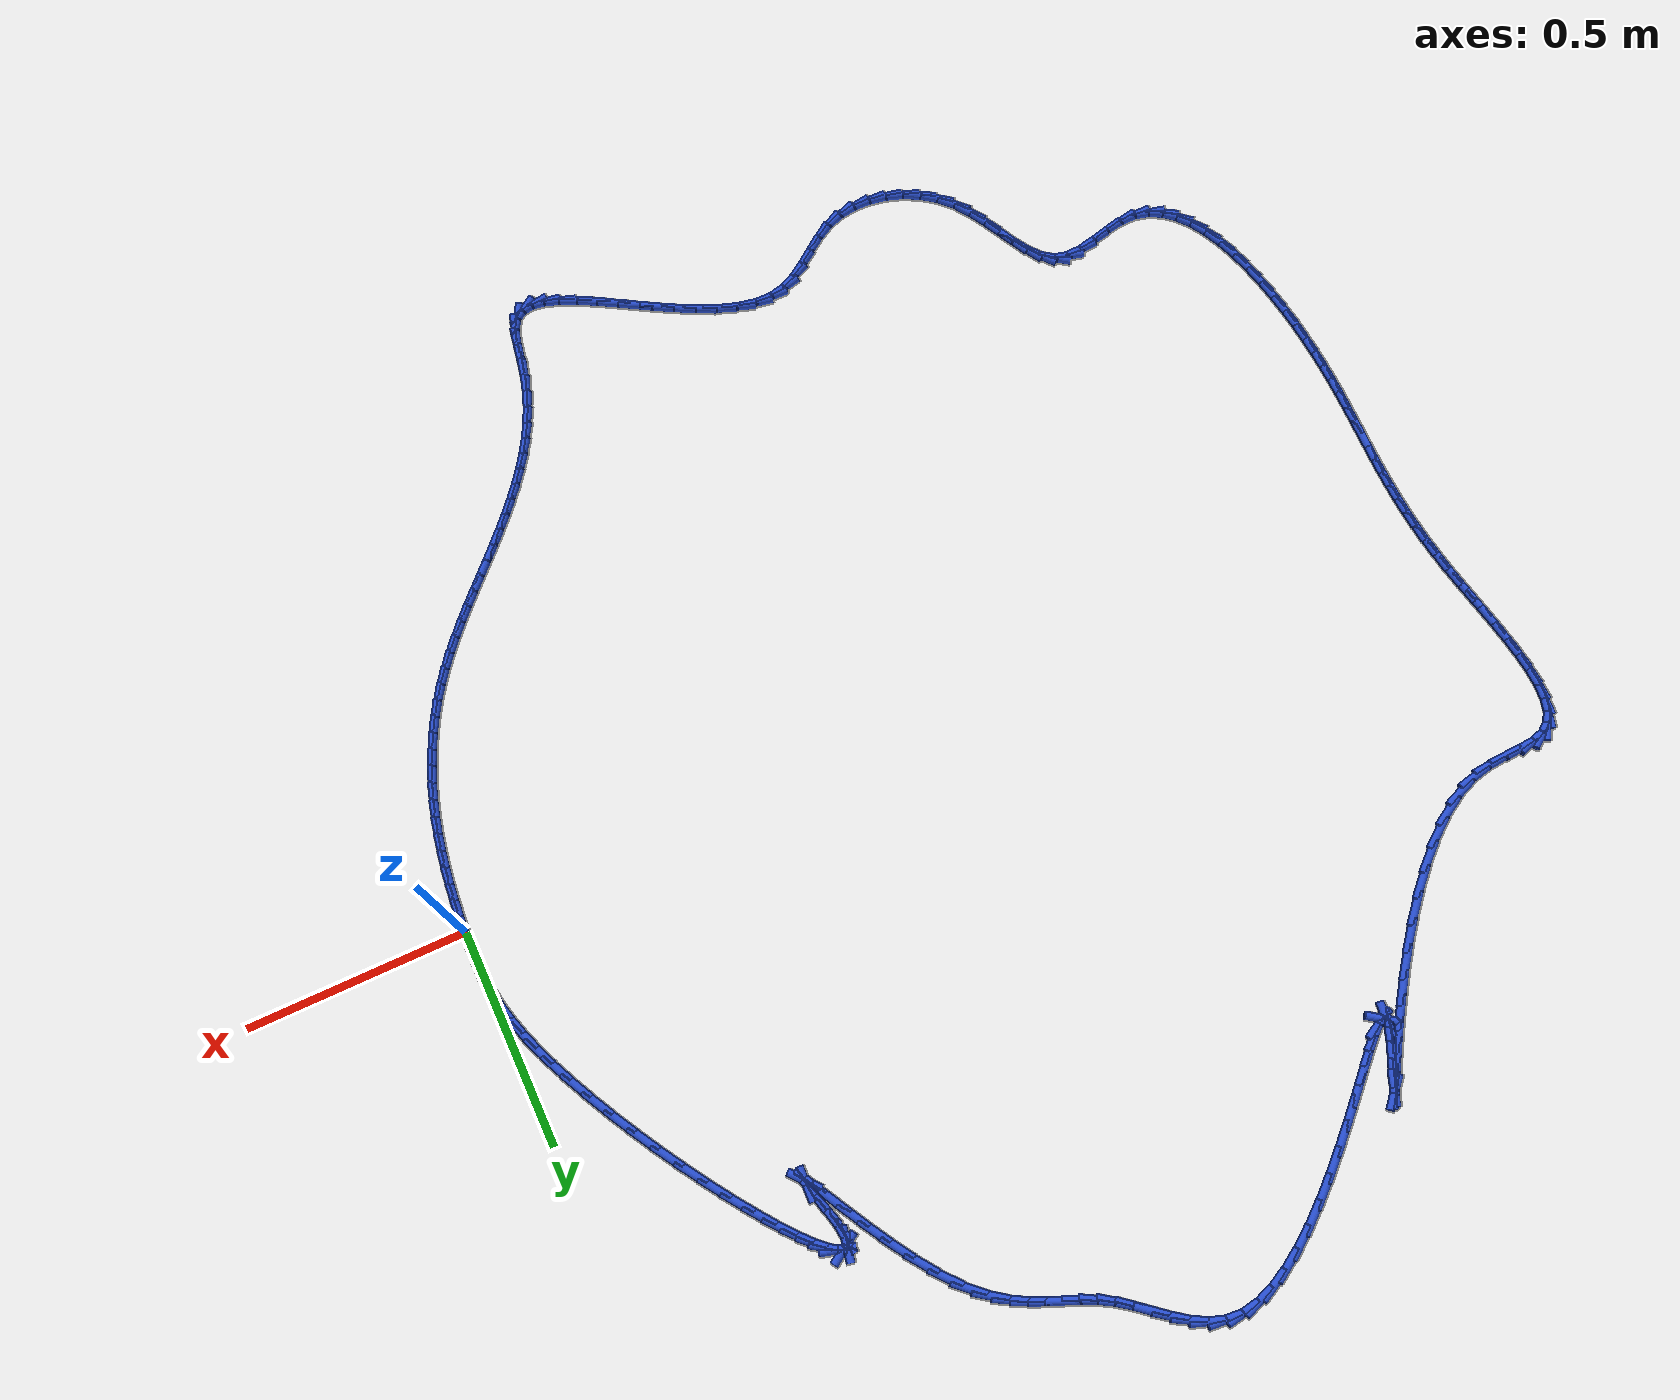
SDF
<sdf version="1.6">
 <world name="default">
  <light name="sun" type="directional">
   <pose>0 0 10 0 -0 0</pose>
   <diffuse>0.8 0.8 0.8 1</diffuse>
   <specular>0.2 0.2 0.2 1</specular>
   <attenuation>
    <range>1000</range>
    <constant>0.9</constant>
    <linear>0.01</linear>
    <quadratic>0.001</quadratic>
   </attenuation>
   <direction>-0.5 0.1 -0.9</direction>
  </light>
  <model name="ground_plane">
   <static>1</static>
   <link name="link">
    <collision name="collision">
     <geometry><plane><normal>0 0 1</normal><size>100 100</size></plane></geometry>
     <surface><friction><ode><mu>100</mu><mu2>50</mu2></ode></friction></surface>
    </collision>
    <visual name="visual">
     <cast_shadows>0</cast_shadows>
     <geometry><plane><normal>0 0 1</normal><size>100 100</size></plane></geometry>
     <material>
      <script><uri>file://media/materials/scripts/gazebo.material</uri><name>Gazebo/WhiteGlow</name></script>
     </material>
    </visual>
   </link>
  </model>
  <gravity>0 0 -9.8</gravity>
  <magnetic_field>6e-06 2.3e-05 -4.2e-05</magnetic_field>
  <atmosphere type="adiabatic"/>
  <physics name="default_physics" default="0" type="ode">
   <max_step_size>0.001</max_step_size>
   <real_time_factor>1</real_time_factor>
   <real_time_update_rate>1000</real_time_update_rate>
  </physics>
  <scene><ambient>0.4 0.4 0.4 1</ambient><background>0.7 0.7 0.7 1</background><shadows>1</shadows></scene>
  <spherical_coordinates>
   <surface_model>EARTH_WGS84</surface_model>
   <latitude_deg>0</latitude_deg>
   <longitude_deg>0</longitude_deg>
   <elevation>0</elevation>
   <heading_deg>0</heading_deg>
  </spherical_coordinates>
  <model name="line">
   <link name="link_0">
    <pose>-2.3852447794681098e-18 -3.469446951953614e-17 0.01 0 1.57 1.536568361687277</pose>
    <collision name="collision">
     <geometry><cylinder><radius>0.01</radius><length>0.08</length></cylinder></geometry>
    </collision>
    <visual name="visual">
     <material>
      <script><name>Gazebo/Blue</name><uri>file://media/materials/scripts/gazebo.material</uri></script>
     </material>
     <geometry><cylinder><radius>0.01</radius><length>0.08</length></cylinder></geometry>
    </visual>
   </link>
   <link name="link_1">
    <pose>0.0012004082090740472 0.03505728102247837 0.01 0 1.57 1.5704771272439422</pose>
    <collision name="collision">
     <geometry><cylinder><radius>0.01</radius><length>0.08</length></cylinder></geometry>
    </collision>
    <visual name="visual">
     <material>
      <script><name>Gazebo/Blue</name><uri>file://media/materials/scripts/gazebo.material</uri></script>
     </material>
     <geometry><cylinder><radius>0.01</radius><length>0.08</length></cylinder></geometry>
    </visual>
   </link>
   <link name="link_2">
    <pose>0.0012114562269414874 0.06966891333582405 0.01 0 1.57 -1.5240608467342291</pose>
    <collision name="collision">
     <geometry><cylinder><radius>0.01</radius><length>0.08</length></cylinder></geometry>
    </collision>
    <visual name="visual">
     <material>
      <script><name>Gazebo/Blue</name><uri>file://media/materials/scripts/gazebo.material</uri></script>
     </material>
     <geometry><cylinder><radius>0.01</radius><length>0.08</length></cylinder></geometry>
    </visual>
   </link>
   <link name="link_3">
    <pose>-0.00041627181827382734 0.10447208157554808 0.01 0 1.57 -1.4668855793598907</pose>
    <collision name="collision">
     <geometry><cylinder><radius>0.01</radius><length>0.08</length></cylinder></geometry>
    </collision>
    <visual name="visual">
     <material>
      <script><name>Gazebo/Blue</name><uri>file://media/materials/scripts/gazebo.material</uri></script>
     </material>
     <geometry><cylinder><radius>0.01</radius><length>0.08</length></cylinder></geometry>
    </visual>
   </link>
   <link name="link_4">
    <pose>-0.004132191798448034 0.14010397037716163 0.01 0 1.57 -1.4037975720328413</pose>
    <collision name="collision">
     <geometry><cylinder><radius>0.01</radius><length>0.08</length></cylinder></geometry>
    </collision>
    <visual name="visual">
     <material>
      <script><name>Gazebo/Blue</name><uri>file://media/materials/scripts/gazebo.material</uri></script>
     </material>
     <geometry><cylinder><radius>0.01</radius><length>0.08</length></cylinder></geometry>
    </visual>
   </link>
   <link name="link_5">
    <pose>-0.010385719585457281 0.1772017643761758 0.01 0 1.57 -1.3392992779858215</pose>
    <collision name="collision">
     <geometry><cylinder><radius>0.01</radius><length>0.08</length></cylinder></geometry>
    </collision>
    <visual name="visual">
     <material>
      <script><name>Gazebo/Blue</name><uri>file://media/materials/scripts/gazebo.material</uri></script>
     </material>
     <geometry><cylinder><radius>0.01</radius><length>0.08</length></cylinder></geometry>
    </visual>
   </link>
   <link name="link_6">
    <pose>-0.019626271051177705 0.21640264820810165 0.01 0 1.57 -1.27727056453285</pose>
    <collision name="collision">
     <geometry><cylinder><radius>0.01</radius><length>0.08</length></cylinder></geometry>
    </collision>
    <visual name="visual">
     <material>
      <script><name>Gazebo/Blue</name><uri>file://media/materials/scripts/gazebo.material</uri></script>
     </material>
     <geometry><cylinder><radius>0.01</radius><length>0.08</length></cylinder></geometry>
    </visual>
   </link>
   <link name="link_7">
    <pose>-0.03230326206748544 0.25834380650845035 0.01 0 1.57 -1.2205641338085151</pose>
    <collision name="collision">
     <geometry><cylinder><radius>0.01</radius><length>0.08</length></cylinder></geometry>
    </collision>
    <visual name="visual">
     <material>
      <script><name>Gazebo/Blue</name><uri>file://media/materials/scripts/gazebo.material</uri></script>
     </material>
     <geometry><cylinder><radius>0.01</radius><length>0.08</length></cylinder></geometry>
    </visual>
   </link>
   <link name="link_8">
    <pose>-0.04884852828851498 0.3036371119326895 0.01 0 1.57 -1.1735904179650758</pose>
    <collision name="collision">
     <geometry><cylinder><radius>0.01</radius><length>0.08</length></cylinder></geometry>
    </collision>
    <visual name="visual">
     <material>
      <script><name>Gazebo/Blue</name><uri>file://media/materials/scripts/gazebo.material</uri></script>
     </material>
     <geometry><cylinder><radius>0.01</radius><length>0.08</length></cylinder></geometry>
    </visual>
   </link>
   <link name="link_9">
    <pose>-0.06923492894647816 0.35223360333986514 0.01 0 1.57 -1.1367071508104774</pose>
    <collision name="collision">
     <geometry><cylinder><radius>0.01</radius><length>0.08</length></cylinder></geometry>
    </collision>
    <visual name="visual">
     <material>
      <script><name>Gazebo/Blue</name><uri>file://media/materials/scripts/gazebo.material</uri></script>
     </material>
     <geometry><cylinder><radius>0.01</radius><length>0.08</length></cylinder></geometry>
    </visual>
   </link>
   <link name="link_10">
    <pose>-0.09294377362127791 0.4033765868878439 0.01 0 1.57 -1.1065521909593512</pose>
    <collision name="collision">
     <geometry><cylinder><radius>0.01</radius><length>0.08</length></cylinder></geometry>
    </collision>
    <visual name="visual">
     <material>
      <script><name>Gazebo/Blue</name><uri>file://media/materials/scripts/gazebo.material</uri></script>
     </material>
     <geometry><cylinder><radius>0.01</radius><length>0.08</length></cylinder></geometry>
    </visual>
   </link>
   <link name="link_11">
    <pose>-0.11943226742696403 0.456274663148498 0.01 0 1.57 -1.0808524294786641</pose>
    <collision name="collision">
     <geometry><cylinder><radius>0.01</radius><length>0.08</length></cylinder></geometry>
    </collision>
    <visual name="visual">
     <material>
      <script><name>Gazebo/Blue</name><uri>file://media/materials/scripts/gazebo.material</uri></script>
     </material>
     <geometry><cylinder><radius>0.01</radius><length>0.08</length></cylinder></geometry>
    </visual>
   </link>
   <link name="link_12">
    <pose>-0.1481576154775864 0.5101364326936998 0.01 0 1.57 -1.0580520031457787</pose>
    <collision name="collision">
     <geometry><cylinder><radius>0.01</radius><length>0.08</length></cylinder></geometry>
    </collision>
    <visual name="visual">
     <material>
      <script><name>Gazebo/Blue</name><uri>file://media/materials/scripts/gazebo.material</uri></script>
     </material>
     <geometry><cylinder><radius>0.01</radius><length>0.08</length></cylinder></geometry>
    </visual>
   </link>
   <link name="link_13">
    <pose>-0.17857702288719468 0.5641704960953212 0.01 0 1.57 -1.0369870157645538</pose>
    <collision name="collision">
     <geometry><cylinder><radius>0.01</radius><length>0.08</length></cylinder></geometry>
    </collision>
    <visual name="visual">
     <material>
      <script><name>Gazebo/Blue</name><uri>file://media/materials/scripts/gazebo.material</uri></script>
     </material>
     <geometry><cylinder><radius>0.01</radius><length>0.08</length></cylinder></geometry>
    </visual>
   </link>
   <link name="link_14">
    <pose>-0.21014769476983877 0.6175854539252348 0.01 0 1.57 -1.016684746605305</pose>
    <collision name="collision">
     <geometry><cylinder><radius>0.01</radius><length>0.08</length></cylinder></geometry>
    </collision>
    <visual name="visual">
     <material>
      <script><name>Gazebo/Blue</name><uri>file://media/materials/scripts/gazebo.material</uri></script>
     </material>
     <geometry><cylinder><radius>0.01</radius><length>0.08</length></cylinder></geometry>
    </visual>
   </link>
   <link name="link_15">
    <pose>-0.2423268362395684 0.6695899067553124 0.01 0 1.57 -0.99621360401622</pose>
    <collision name="collision">
     <geometry><cylinder><radius>0.01</radius><length>0.08</length></cylinder></geometry>
    </collision>
    <visual name="visual">
     <material>
      <script><name>Gazebo/Blue</name><uri>file://media/materials/scripts/gazebo.material</uri></script>
     </material>
     <geometry><cylinder><radius>0.01</radius><length>0.08</length></cylinder></geometry>
    </visual>
   </link>
   <link name="link_16">
    <pose>-0.2745716524104334 0.7193924551574266 0.01 0 1.57 -0.9745345805380871</pose>
    <collision name="collision">
     <geometry><cylinder><radius>0.01</radius><length>0.08</length></cylinder></geometry>
    </collision>
    <visual name="visual">
     <material>
      <script><name>Gazebo/Blue</name><uri>file://media/materials/scripts/gazebo.material</uri></script>
     </material>
     <geometry><cylinder><radius>0.01</radius><length>0.08</length></cylinder></geometry>
    </visual>
   </link>
   <link name="link_17">
    <pose>-0.3063393483964836 0.7662016997034492 0.01 0 1.57 -0.950301166007441</pose>
    <collision name="collision">
     <geometry><cylinder><radius>0.01</radius><length>0.08</length></cylinder></geometry>
    </collision>
    <visual name="visual">
     <material>
      <script><name>Gazebo/Blue</name><uri>file://media/materials/scripts/gazebo.material</uri></script>
     </material>
     <geometry><cylinder><radius>0.01</radius><length>0.08</length></cylinder></geometry>
    </visual>
   </link>
   <link name="link_18">
    <pose>-0.33708712931176865 0.8092262409652528 0.01 0 1.57 -0.9215154018738458</pose>
    <collision name="collision">
     <geometry><cylinder><radius>0.01</radius><length>0.08</length></cylinder></geometry>
    </collision>
    <visual name="visual">
     <material>
      <script><name>Gazebo/Blue</name><uri>file://media/materials/scripts/gazebo.material</uri></script>
     </material>
     <geometry><cylinder><radius>0.01</radius><length>0.08</length></cylinder></geometry>
    </visual>
   </link>
   <link name="link_19">
    <pose>-0.3662722002703386 0.8476746795147095 0.01 0 1.57 -0.8848252127844743</pose>
    <collision name="collision">
     <geometry><cylinder><radius>0.01</radius><length>0.08</length></cylinder></geometry>
    </collision>
    <visual name="visual">
     <material>
      <script><name>Gazebo/Blue</name><uri>file://media/materials/scripts/gazebo.material</uri></script>
     </material>
     <geometry><cylinder><radius>0.01</radius><length>0.08</length></cylinder></geometry>
    </visual>
   </link>
   <link name="link_20">
    <pose>-0.393351766386243 0.8807556159236913 0.01 0 1.57 -0.8338627794343835</pose>
    <collision name="collision">
     <geometry><cylinder><radius>0.01</radius><length>0.08</length></cylinder></geometry>
    </collision>
    <visual name="visual">
     <material>
      <script><name>Gazebo/Blue</name><uri>file://media/materials/scripts/gazebo.material</uri></script>
     </material>
     <geometry><cylinder><radius>0.01</radius><length>0.08</length></cylinder></geometry>
    </visual>
   </link>
   <link name="link_21">
    <pose>-0.4177830327735318 0.9076776507640707 0.01 0 1.57 -0.7546294425116679</pose>
    <collision name="collision">
     <geometry><cylinder><radius>0.01</radius><length>0.08</length></cylinder></geometry>
    </collision>
    <visual name="visual">
     <material>
      <script><name>Gazebo/Blue</name><uri>file://media/materials/scripts/gazebo.material</uri></script>
     </material>
     <geometry><cylinder><radius>0.01</radius><length>0.08</length></cylinder></geometry>
    </visual>
   </link>
   <link name="link_22">
    <pose>-0.43902320454625454 0.9276493846077196 0.01 0 1.57 -0.6097913006778211</pose>
    <collision name="collision">
     <geometry><cylinder><radius>0.01</radius><length>0.08</length></cylinder></geometry>
    </collision>
    <visual name="visual">
     <material>
      <script><name>Gazebo/Blue</name><uri>file://media/materials/scripts/gazebo.material</uri></script>
     </material>
     <geometry><cylinder><radius>0.01</radius><length>0.08</length></cylinder></geometry>
    </visual>
   </link>
   <link name="link_23">
    <pose>-0.4565294868184614 0.9398794180265105 0.01 0 1.57 -0.2724931772572617</pose>
    <collision name="collision">
     <geometry><cylinder><radius>0.01</radius><length>0.08</length></cylinder></geometry>
    </collision>
    <visual name="visual">
     <material>
      <script><name>Gazebo/Blue</name><uri>file://media/materials/scripts/gazebo.material</uri></script>
     </material>
     <geometry><cylinder><radius>0.01</radius><length>0.08</length></cylinder></geometry>
    </visual>
   </link>
   <link name="link_24">
    <pose>-0.4697590847042017 0.943576351592315 0.01 0 1.57 0.5897145132117619</pose>
    <collision name="collision">
     <geometry><cylinder><radius>0.01</radius><length>0.08</length></cylinder></geometry>
    </collision>
    <visual name="visual">
     <material>
      <script><name>Gazebo/Blue</name><uri>file://media/materials/scripts/gazebo.material</uri></script>
     </material>
     <geometry><cylinder><radius>0.01</radius><length>0.08</length></cylinder></geometry>
    </visual>
   </link>
   <link name="link_25">
    <pose>-0.47816920331752594 0.9379487858770065 0.01 0 1.57 1.379567644341341</pose>
    <collision name="collision">
     <geometry><cylinder><radius>0.01</radius><length>0.08</length></cylinder></geometry>
    </collision>
    <visual name="visual">
     <material>
      <script><name>Gazebo/Blue</name><uri>file://media/materials/scripts/gazebo.material</uri></script>
     </material>
     <geometry><cylinder><radius>0.01</radius><length>0.08</length></cylinder></geometry>
    </visual>
   </link>
   <link name="link_26">
    <pose>-0.4812170477724832 0.9222053214524562 0.01 0 1.57 -1.4639944097389546</pose>
    <collision name="collision">
     <geometry><cylinder><radius>0.01</radius><length>0.08</length></cylinder></geometry>
    </collision>
    <visual name="visual">
     <material>
      <script><name>Gazebo/Blue</name><uri>file://media/materials/scripts/gazebo.material</uri></script>
     </material>
     <geometry><cylinder><radius>0.01</radius><length>0.08</length></cylinder></geometry>
    </visual>
   </link>
   <link name="link_27">
    <pose>-0.47835982318312364 0.8955545588905367 0.01 0 1.57 -1.3381597056038583</pose>
    <collision name="collision">
     <geometry><cylinder><radius>0.01</radius><length>0.08</length></cylinder></geometry>
    </collision>
    <visual name="visual">
     <material>
      <script><name>Gazebo/Blue</name><uri>file://media/materials/scripts/gazebo.material</uri></script>
     </material>
     <geometry><cylinder><radius>0.01</radius><length>0.08</length></cylinder></geometry>
    </visual>
   </link>
   <link name="link_28">
    <pose>-0.46950901822485164 0.8581977664622289 0.01 0 1.57 -1.2982125872773014</pose>
    <collision name="collision">
     <geometry><cylinder><radius>0.01</radius><length>0.08</length></cylinder></geometry>
    </collision>
    <visual name="visual">
     <material>
      <script><name>Gazebo/Blue</name><uri>file://media/materials/scripts/gazebo.material</uri></script>
     </material>
     <geometry><cylinder><radius>0.01</radius><length>0.08</length></cylinder></geometry>
    </visual>
   </link>
   <link name="link_29">
    <pose>-0.45856823571531413 0.8190594925597314 0.01 0 1.57 -1.3189017724294652</pose>
    <collision name="collision">
     <geometry><cylinder><radius>0.01</radius><length>0.08</length></cylinder></geometry>
    </collision>
    <visual name="visual">
     <material>
      <script><name>Gazebo/Blue</name><uri>file://media/materials/scripts/gazebo.material</uri></script>
     </material>
     <geometry><cylinder><radius>0.01</radius><length>0.08</length></cylinder></geometry>
    </visual>
   </link>
   <link name="link_30">
    <pose>-0.4514762203615382 0.791502807825515 0.01 0 1.57 1.539509314190848</pose>
    <collision name="collision">
     <geometry><cylinder><radius>0.01</radius><length>0.08</length></cylinder></geometry>
    </collision>
    <visual name="visual">
     <material>
      <script><name>Gazebo/Blue</name><uri>file://media/materials/scripts/gazebo.material</uri></script>
     </material>
     <geometry><cylinder><radius>0.01</radius><length>0.08</length></cylinder></geometry>
    </visual>
   </link>
   <link name="link_31">
    <pose>-0.4517419446303152 0.7830124619214686 0.01 0 1.57 -0.870355206022637</pose>
    <collision name="collision">
     <geometry><cylinder><radius>0.01</radius><length>0.08</length></cylinder></geometry>
    </collision>
    <visual name="visual">
     <material>
      <script><name>Gazebo/Blue</name><uri>file://media/materials/scripts/gazebo.material</uri></script>
     </material>
     <geometry><cylinder><radius>0.01</radius><length>0.08</length></cylinder></geometry>
    </visual>
   </link>
   <link name="link_32">
    <pose>-0.4589312431201624 0.7915402603295756 0.01 0 1.57 -1.0388316380422888</pose>
    <collision name="collision">
     <geometry><cylinder><radius>0.01</radius><length>0.08</length></cylinder></geometry>
    </collision>
    <visual name="visual">
     <material>
      <script><name>Gazebo/Blue</name><uri>file://media/materials/scripts/gazebo.material</uri></script>
     </material>
     <geometry><cylinder><radius>0.01</radius><length>0.08</length></cylinder></geometry>
    </visual>
   </link>
   <link name="link_33">
    <pose>-0.4722526365195251 0.8141741651478928 0.01 0 1.57 -1.0666689024938116</pose>
    <collision name="collision">
     <geometry><cylinder><radius>0.01</radius><length>0.08</length></cylinder></geometry>
    </collision>
    <visual name="visual">
     <material>
      <script><name>Gazebo/Blue</name><uri>file://media/materials/scripts/gazebo.material</uri></script>
     </material>
     <geometry><cylinder><radius>0.01</radius><length>0.08</length></cylinder></geometry>
    </visual>
   </link>
   <link name="link_34">
    <pose>-0.49091464551684816 0.8480021384744763 0.01 0 1.57 -1.0670302537280683</pose>
    <collision name="collision">
     <geometry><cylinder><radius>0.01</radius><length>0.08</length></cylinder></geometry>
    </collision>
    <visual name="visual">
     <material>
      <script><name>Gazebo/Blue</name><uri>file://media/materials/scripts/gazebo.material</uri></script>
     </material>
     <geometry><cylinder><radius>0.01</radius><length>0.08</length></cylinder></geometry>
    </visual>
   </link>
   <link name="link_35">
    <pose>-0.5141257908005769 0.8901121424073829 0.01 0 1.57 -1.054236030854977</pose>
    <collision name="collision">
     <geometry><cylinder><radius>0.01</radius><length>0.08</length></cylinder></geometry>
    </collision>
    <visual name="visual">
     <material>
      <script><name>Gazebo/Blue</name><uri>file://media/materials/scripts/gazebo.material</uri></script>
     </material>
     <geometry><cylinder><radius>0.01</radius><length>0.08</length></cylinder></geometry>
    </visual>
   </link>
   <link name="link_36">
    <pose>-0.541094593059156 0.9375921390446683 0.01 0 1.57 -1.0307861251179917</pose>
    <collision name="collision">
     <geometry><cylinder><radius>0.01</radius><length>0.08</length></cylinder></geometry>
    </collision>
    <visual name="visual">
     <material>
      <script><name>Gazebo/Blue</name><uri>file://media/materials/scripts/gazebo.material</uri></script>
     </material>
     <geometry><cylinder><radius>0.01</radius><length>0.08</length></cylinder></geometry>
    </visual>
   </link>
   <link name="link_37">
    <pose>-0.5710295729810311 0.9875300904843897 0.01 0 1.57 -0.9952005250413384</pose>
    <collision name="collision">
     <geometry><cylinder><radius>0.01</radius><length>0.08</length></cylinder></geometry>
    </collision>
    <visual name="visual">
     <material>
      <script><name>Gazebo/Blue</name><uri>file://media/materials/scripts/gazebo.material</uri></script>
     </material>
     <geometry><cylinder><radius>0.01</radius><length>0.08</length></cylinder></geometry>
    </visual>
   </link>
   <link name="link_38">
    <pose>-0.6031392512546468 1.037013958824603 0.01 0 1.57 -0.9426709413316726</pose>
    <collision name="collision">
     <geometry><cylinder><radius>0.01</radius><length>0.08</length></cylinder></geometry>
    </collision>
    <visual name="visual">
     <material>
      <script><name>Gazebo/Blue</name><uri>file://media/materials/scripts/gazebo.material</uri></script>
     </material>
     <geometry><cylinder><radius>0.01</radius><length>0.08</length></cylinder></geometry>
    </visual>
   </link>
   <link name="link_39">
    <pose>-0.6366321485684485 1.0831317061633643 0.01 0 1.57 -0.8630929056633433</pose>
    <collision name="collision">
     <geometry><cylinder><radius>0.01</radius><length>0.08</length></cylinder></geometry>
    </collision>
    <visual name="visual">
     <material>
      <script><name>Gazebo/Blue</name><uri>file://media/materials/scripts/gazebo.material</uri></script>
     </material>
     <geometry><cylinder><radius>0.01</radius><length>0.08</length></cylinder></geometry>
    </visual>
   </link>
   <link name="link_40">
    <pose>-0.6707168179998384 1.1229715028209317 0.01 0 1.57 -0.7481307942963765</pose>
    <collision name="collision">
     <geometry><cylinder><radius>0.01</radius><length>0.08</length></cylinder></geometry>
    </collision>
    <visual name="visual">
     <material>
      <script><name>Gazebo/Blue</name><uri>file://media/materials/scripts/gazebo.material</uri></script>
     </material>
     <geometry><cylinder><radius>0.01</radius><length>0.08</length></cylinder></geometry>
    </visual>
   </link>
   <link name="link_41">
    <pose>-0.7047470712711574 1.1545553582160215 0.01 0 1.57 -0.625735015658876</pose>
    <collision name="collision">
     <geometry><cylinder><radius>0.01</radius><length>0.08</length></cylinder></geometry>
    </collision>
    <visual name="visual">
     <material>
      <script><name>Gazebo/Blue</name><uri>file://media/materials/scripts/gazebo.material</uri></script>
     </material>
     <geometry><cylinder><radius>0.01</radius><length>0.08</length></cylinder></geometry>
    </visual>
   </link>
   <link name="link_42">
    <pose>-0.7385558777556922 1.178985691535526 0.01 0 1.57 -0.5159869314029824</pose>
    <collision name="collision">
     <geometry><cylinder><radius>0.01</radius><length>0.08</length></cylinder></geometry>
    </collision>
    <visual name="visual">
     <material>
      <script><name>Gazebo/Blue</name><uri>file://media/materials/scripts/gazebo.material</uri></script>
     </material>
     <geometry><cylinder><radius>0.01</radius><length>0.08</length></cylinder></geometry>
    </visual>
   </link>
   <link name="link_43">
    <pose>-0.772074865947716 1.1979991819419553 0.01 0 1.57 -0.43311215887693355</pose>
    <collision name="collision">
     <geometry><cylinder><radius>0.01</radius><length>0.08</length></cylinder></geometry>
    </collision>
    <visual name="visual">
     <material>
      <script><name>Gazebo/Blue</name><uri>file://media/materials/scripts/gazebo.material</uri></script>
     </material>
     <geometry><cylinder><radius>0.01</radius><length>0.08</length></cylinder></geometry>
    </visual>
   </link>
   <link name="link_44">
    <pose>-0.8052356643415015 1.2133325085978182 0.01 0 1.57 -0.388281118846768</pose>
    <collision name="collision">
     <geometry><cylinder><radius>0.01</radius><length>0.08</length></cylinder></geometry>
    </collision>
    <visual name="visual">
     <material>
      <script><name>Gazebo/Blue</name><uri>file://media/materials/scripts/gazebo.material</uri></script>
     </material>
     <geometry><cylinder><radius>0.01</radius><length>0.08</length></cylinder></geometry>
    </visual>
   </link>
   <link name="link_45">
    <pose>-0.8379699014313224 1.2267223506656253 0.01 0 1.57 -0.38816540189397314</pose>
    <collision name="collision">
     <geometry><cylinder><radius>0.01</radius><length>0.08</length></cylinder></geometry>
    </collision>
    <visual name="visual">
     <material>
      <script><name>Gazebo/Blue</name><uri>file://media/materials/scripts/gazebo.material</uri></script>
     </material>
     <geometry><cylinder><radius>0.01</radius><length>0.08</length></cylinder></geometry>
    </visual>
   </link>
   <link name="link_46">
    <pose>-0.8702092057114514 1.239905387307886 0.01 0 1.57 -0.434831123835856</pose>
    <collision name="collision">
     <geometry><cylinder><radius>0.01</radius><length>0.08</length></cylinder></geometry>
    </collision>
    <visual name="visual">
     <material>
      <script><name>Gazebo/Blue</name><uri>file://media/materials/scripts/gazebo.material</uri></script>
     </material>
     <geometry><cylinder><radius>0.01</radius><length>0.08</length></cylinder></geometry>
    </visual>
   </link>
   <link name="link_47">
    <pose>-0.9018852056761617 1.2546182976871103 0.01 0 1.57 -0.5249508858070039</pose>
    <collision name="collision">
     <geometry><cylinder><radius>0.01</radius><length>0.08</length></cylinder></geometry>
    </collision>
    <visual name="visual">
     <material>
      <script><name>Gazebo/Blue</name><uri>file://media/materials/scripts/gazebo.material</uri></script>
     </material>
     <geometry><cylinder><radius>0.01</radius><length>0.08</length></cylinder></geometry>
    </visual>
   </link>
   <link name="link_48">
    <pose>-0.9329295303087153 1.2725977577600767 0.01 0 1.57 -0.6314821438073815</pose>
    <collision name="collision">
     <geometry><cylinder><radius>0.01</radius><length>0.08</length></cylinder></geometry>
    </collision>
    <visual name="visual">
     <material>
      <script><name>Gazebo/Blue</name><uri>file://media/materials/scripts/gazebo.material</uri></script>
     </material>
     <geometry><cylinder><radius>0.01</radius><length>0.08</length></cylinder></geometry>
    </visual>
   </link>
   <link name="link_49">
    <pose>-0.963382116963484 1.294870391382647 0.01 0 1.57 -0.6875152324769321</pose>
    <collision name="collision">
     <geometry><cylinder><radius>0.01</radius><length>0.08</length></cylinder></geometry>
    </collision>
    <visual name="visual">
     <material>
      <script><name>Gazebo/Blue</name><uri>file://media/materials/scripts/gazebo.material</uri></script>
     </material>
     <geometry><cylinder><radius>0.01</radius><length>0.08</length></cylinder></geometry>
    </visual>
   </link>
   <link name="link_50">
    <pose>-0.9936948429544761 1.3197622108993552 0.01 0 1.57 -0.6868659327365862</pose>
    <collision name="collision">
     <geometry><cylinder><radius>0.01</radius><length>0.08</length></cylinder></geometry>
    </collision>
    <visual name="visual">
     <material>
      <script><name>Gazebo/Blue</name><uri>file://media/materials/scripts/gazebo.material</uri></script>
     </material>
     <geometry><cylinder><radius>0.01</radius><length>0.08</length></cylinder></geometry>
    </visual>
   </link>
   <link name="link_51">
    <pose>-1.024417506389878 1.344957275822134 0.01 0 1.57 -0.6316932384821966</pose>
    <collision name="collision">
     <geometry><cylinder><radius>0.01</radius><length>0.08</length></cylinder></geometry>
    </collision>
    <visual name="visual">
     <material>
      <script><name>Gazebo/Blue</name><uri>file://media/materials/scripts/gazebo.material</uri></script>
     </material>
     <geometry><cylinder><radius>0.01</radius><length>0.08</length></cylinder></geometry>
    </visual>
   </link>
   <link name="link_52">
    <pose>-1.0560999053778746 1.368139645662913 0.01 0 1.57 -0.5165740031825229</pose>
    <collision name="collision">
     <geometry><cylinder><radius>0.01</radius><length>0.08</length></cylinder></geometry>
    </collision>
    <visual name="visual">
     <material>
      <script><name>Gazebo/Blue</name><uri>file://media/materials/scripts/gazebo.material</uri></script>
     </material>
     <geometry><cylinder><radius>0.01</radius><length>0.08</length></cylinder></geometry>
    </visual>
   </link>
   <link name="link_53">
    <pose>-1.0892918380266514 1.386993379933624 0.01 0 1.57 -0.3334164865474294</pose>
    <collision name="collision">
     <geometry><cylinder><radius>0.01</radius><length>0.08</length></cylinder></geometry>
    </collision>
    <visual name="visual">
     <material>
      <script><name>Gazebo/Blue</name><uri>file://media/materials/scripts/gazebo.material</uri></script>
     </material>
     <geometry><cylinder><radius>0.01</radius><length>0.08</length></cylinder></geometry>
    </visual>
   </link>
   <link name="link_54">
    <pose>-1.1245431024443944 1.3992025381461979 0.01 0 1.57 -0.0858396317318175</pose>
    <collision name="collision">
     <geometry><cylinder><radius>0.01</radius><length>0.08</length></cylinder></geometry>
    </collision>
    <visual name="visual">
     <material>
      <script><name>Gazebo/Blue</name><uri>file://media/materials/scripts/gazebo.material</uri></script>
     </material>
     <geometry><cylinder><radius>0.01</radius><length>0.08</length></cylinder></geometry>
    </visual>
   </link>
   <link name="link_55">
    <pose>-1.162400563305171 1.4024602139100877 0.01 0 1.57 0.16693792970148782</pose>
    <collision name="collision">
     <geometry><cylinder><radius>0.01</radius><length>0.08</length></cylinder></geometry>
    </collision>
    <visual name="visual">
     <material>
      <script><name>Gazebo/Blue</name><uri>file://media/materials/scripts/gazebo.material</uri></script>
     </material>
     <geometry><cylinder><radius>0.01</radius><length>0.08</length></cylinder></geometry>
    </visual>
   </link>
   <link name="link_56">
    <pose>-1.203036604209944 1.3956127902556665 0.01 0 1.57 0.35394991808956044</pose>
    <collision name="collision">
     <geometry><cylinder><radius>0.01</radius><length>0.08</length></cylinder></geometry>
    </collision>
    <visual name="visual">
     <material>
      <script><name>Gazebo/Blue</name><uri>file://media/materials/scripts/gazebo.material</uri></script>
     </material>
     <geometry><cylinder><radius>0.01</radius><length>0.08</length></cylinder></geometry>
    </visual>
   </link>
   <link name="link_57">
    <pose>-1.2458855593814564 1.3797796210018072 0.01 0 1.57 0.4855371796997167</pose>
    <collision name="collision">
     <geometry><cylinder><radius>0.01</radius><length>0.08</length></cylinder></geometry>
    </collision>
    <visual name="visual">
     <material>
      <script><name>Gazebo/Blue</name><uri>file://media/materials/scripts/gazebo.material</uri></script>
     </material>
     <geometry><cylinder><radius>0.01</radius><length>0.08</length></cylinder></geometry>
    </visual>
   </link>
   <link name="link_58">
    <pose>-1.2902954458621239 1.356345891001485 0.01 0 1.57 0.5793456564147746</pose>
    <collision name="collision">
     <geometry><cylinder><radius>0.01</radius><length>0.08</length></cylinder></geometry>
    </collision>
    <visual name="visual">
     <material>
      <script><name>Gazebo/Blue</name><uri>file://media/materials/scripts/gazebo.material</uri></script>
     </material>
     <geometry><cylinder><radius>0.01</radius><length>0.08</length></cylinder></geometry>
    </visual>
   </link>
   <link name="link_59">
    <pose>-1.3356142806943627 1.3266967851076743 0.01 0 1.57 0.6476649487768694</pose>
    <collision name="collision">
     <geometry><cylinder><radius>0.01</radius><length>0.08</length></cylinder></geometry>
    </collision>
    <visual name="visual">
     <material>
      <script><name>Gazebo/Blue</name><uri>file://media/materials/scripts/gazebo.material</uri></script>
     </material>
     <geometry><cylinder><radius>0.01</radius><length>0.08</length></cylinder></geometry>
    </visual>
   </link>
   <link name="link_60">
    <pose>-1.3811900809205886 1.2922174881733506 0.01 0 1.57 0.6983021492797159</pose>
    <collision name="collision">
     <geometry><cylinder><radius>0.01</radius><length>0.08</length></cylinder></geometry>
    </collision>
    <visual name="visual">
     <material>
      <script><name>Gazebo/Blue</name><uri>file://media/materials/scripts/gazebo.material</uri></script>
     </material>
     <geometry><cylinder><radius>0.01</radius><length>0.08</length></cylinder></geometry>
    </visual>
   </link>
   <link name="link_61">
    <pose>-1.426370863583217 1.2542931850514876 0.01 0 1.57 0.7361066799409663</pose>
    <collision name="collision">
     <geometry><cylinder><radius>0.01</radius><length>0.08</length></cylinder></geometry>
    </collision>
    <visual name="visual">
     <material>
      <script><name>Gazebo/Blue</name><uri>file://media/materials/scripts/gazebo.material</uri></script>
     </material>
     <geometry><cylinder><radius>0.01</radius><length>0.08</length></cylinder></geometry>
    </visual>
   </link>
   <link name="link_62">
    <pose>-1.470504645724664 1.2143090605950613 0.01 0 1.57 0.7640274657303006</pose>
    <collision name="collision">
     <geometry><cylinder><radius>0.01</radius><length>0.08</length></cylinder></geometry>
    </collision>
    <visual name="visual">
     <material>
      <script><name>Gazebo/Blue</name><uri>file://media/materials/scripts/gazebo.material</uri></script>
     </material>
     <geometry><cylinder><radius>0.01</radius><length>0.08</length></cylinder></geometry>
    </visual>
   </link>
   <link name="link_63">
    <pose>-1.5129394443873463 1.1736502996570457 0.01 0 1.57 0.7837035980487882</pose>
    <collision name="collision">
     <geometry><cylinder><radius>0.01</radius><length>0.08</length></cylinder></geometry>
    </collision>
    <visual name="visual">
     <material>
      <script><name>Gazebo/Blue</name><uri>file://media/materials/scripts/gazebo.material</uri></script>
     </material>
     <geometry><cylinder><radius>0.01</radius><length>0.08</length></cylinder></geometry>
    </visual>
   </link>
   <link name="link_64">
    <pose>-1.553023276613678 1.1337020870904155 0.01 0 1.57 0.7956949019707528</pose>
    <collision name="collision">
     <geometry><cylinder><radius>0.01</radius><length>0.08</length></cylinder></geometry>
    </collision>
    <visual name="visual">
     <material>
      <script><name>Gazebo/Blue</name><uri>file://media/materials/scripts/gazebo.material</uri></script>
     </material>
     <geometry><cylinder><radius>0.01</radius><length>0.08</length></cylinder></geometry>
    </visual>
   </link>
   <link name="link_65">
    <pose>-1.5901041594460763 1.0958496077481459 0.01 0 1.57 0.7993448326599367</pose>
    <collision name="collision">
     <geometry><cylinder><radius>0.01</radius><length>0.08</length></cylinder></geometry>
    </collision>
    <visual name="visual">
     <material>
      <script><name>Gazebo/Blue</name><uri>file://media/materials/scripts/gazebo.material</uri></script>
     </material>
     <geometry><cylinder><radius>0.01</radius><length>0.08</length></cylinder></geometry>
    </visual>
   </link>
   <link name="link_66">
    <pose>-1.6235301099269572 1.0614780464832114 0.01 0 1.57 0.7919895647633824</pose>
    <collision name="collision">
     <geometry><cylinder><radius>0.01</radius><length>0.08</length></cylinder></geometry>
    </collision>
    <visual name="visual">
     <material>
      <script><name>Gazebo/Blue</name><uri>file://media/materials/scripts/gazebo.material</uri></script>
     </material>
     <geometry><cylinder><radius>0.01</radius><length>0.08</length></cylinder></geometry>
    </visual>
   </link>
   <link name="link_67">
    <pose>-1.6526491450987362 1.031972588148587 0.01 0 1.57 0.7662930415040041</pose>
    <collision name="collision">
     <geometry><cylinder><radius>0.01</radius><length>0.08</length></cylinder></geometry>
    </collision>
    <visual name="visual">
     <material>
      <script><name>Gazebo/Blue</name><uri>file://media/materials/scripts/gazebo.material</uri></script>
     </material>
     <geometry><cylinder><radius>0.01</radius><length>0.08</length></cylinder></geometry>
    </visual>
   </link>
   <link name="link_68">
    <pose>-1.6768092820038292 1.0087184175972472 0.01 0 1.57 0.6998068181346495</pose>
    <collision name="collision">
     <geometry><cylinder><radius>0.01</radius><length>0.08</length></cylinder></geometry>
    </collision>
    <visual name="visual">
     <material>
      <script><name>Gazebo/Blue</name><uri>file://media/materials/scripts/gazebo.material</uri></script>
     </material>
     <geometry><cylinder><radius>0.01</radius><length>0.08</length></cylinder></geometry>
    </visual>
   </link>
   <link name="link_69">
    <pose>-1.6953585376846514 0.9931007196821666 0.01 0 1.57 0.49269697560730286</pose>
    <collision name="collision">
     <geometry><cylinder><radius>0.01</radius><length>0.08</length></cylinder></geometry>
    </collision>
    <visual name="visual">
     <material>
      <script><name>Gazebo/Blue</name><uri>file://media/materials/scripts/gazebo.material</uri></script>
     </material>
     <geometry><cylinder><radius>0.01</radius><length>0.08</length></cylinder></geometry>
    </visual>
   </link>
   <link name="link_70">
    <pose>-1.7076449291836198 0.9865046792563205 0.01 0 1.57 -0.6170351477215499</pose>
    <collision name="collision">
     <geometry><cylinder><radius>0.01</radius><length>0.08</length></cylinder></geometry>
    </collision>
    <visual name="visual">
     <material>
      <script><name>Gazebo/Blue</name><uri>file://media/materials/scripts/gazebo.material</uri></script>
     </material>
     <geometry><cylinder><radius>0.01</radius><length>0.08</length></cylinder></geometry>
    </visual>
   </link>
   <link name="link_71">
    <pose>-1.7130164735431497 0.9903154811726835 0.01 0 1.57 1.4310159387744144</pose>
    <collision name="collision">
     <geometry><cylinder><radius>0.01</radius><length>0.08</length></cylinder></geometry>
    </collision>
    <visual name="visual">
     <material>
      <script><name>Gazebo/Blue</name><uri>file://media/materials/scripts/gazebo.material</uri></script>
     </material>
     <geometry><cylinder><radius>0.01</radius><length>0.08</length></cylinder></geometry>
    </visual>
   </link>
   <link name="link_72">
    <pose>-1.7108211878056565 1.0059183102842302 0.01 0 1.57 1.2247098024166136</pose>
    <collision name="collision">
     <geometry><cylinder><radius>0.01</radius><length>0.08</length></cylinder></geometry>
    </collision>
    <visual name="visual">
     <material>
      <script><name>Gazebo/Blue</name><uri>file://media/materials/scripts/gazebo.material</uri></script>
     </material>
     <geometry><cylinder><radius>0.01</radius><length>0.08</length></cylinder></geometry>
    </visual>
   </link>
   <link name="link_73">
    <pose>-1.700518190233851 1.034490138680337 0.01 0 1.57 1.1655637904282132</pose>
    <collision name="collision">
     <geometry><cylinder><radius>0.01</radius><length>0.08</length></cylinder></geometry>
    </collision>
    <visual name="visual">
     <material>
      <script><name>Gazebo/Blue</name><uri>file://media/materials/scripts/gazebo.material</uri></script>
     </material>
     <geometry><cylinder><radius>0.01</radius><length>0.08</length></cylinder></geometry>
    </visual>
   </link>
   <link name="link_74">
    <pose>-1.684763125091963 1.071217387573205 0.01 0 1.57 1.149024315685371</pose>
    <collision name="collision">
     <geometry><cylinder><radius>0.01</radius><length>0.08</length></cylinder></geometry>
    </collision>
    <visual name="visual">
     <material>
      <script><name>Gazebo/Blue</name><uri>file://media/materials/scripts/gazebo.material</uri></script>
     </material>
     <geometry><cylinder><radius>0.01</radius><length>0.08</length></cylinder></geometry>
    </visual>
   </link>
   <link name="link_75">
    <pose>-1.669809793137913 1.1045433164612342 0.01 0 1.57 1.1559700363063237</pose>
    <collision name="collision">
     <geometry><cylinder><radius>0.01</radius><length>0.08</length></cylinder></geometry>
    </collision>
    <visual name="visual">
     <material>
      <script><name>Gazebo/Blue</name><uri>file://media/materials/scripts/gazebo.material</uri></script>
     </material>
     <geometry><cylinder><radius>0.01</radius><length>0.08</length></cylinder></geometry>
    </visual>
   </link>
   <link name="link_76">
    <pose>-1.6605810753970143 1.1254995141115947 0.01 0 1.57 1.2170434990509773</pose>
    <collision name="collision">
     <geometry><cylinder><radius>0.01</radius><length>0.08</length></cylinder></geometry>
    </collision>
    <visual name="visual">
     <material>
      <script><name>Gazebo/Blue</name><uri>file://media/materials/scripts/gazebo.material</uri></script>
     </material>
     <geometry><cylinder><radius>0.01</radius><length>0.08</length></cylinder></geometry>
    </visual>
   </link>
   <link name="link_77">
    <pose>-1.6575183772066797 1.133793053617388 0.01 0 1.57 0.8456377064191734</pose>
    <collision name="collision">
     <geometry><cylinder><radius>0.01</radius><length>0.08</length></cylinder></geometry>
    </collision>
    <visual name="visual">
     <material>
      <script><name>Gazebo/Blue</name><uri>file://media/materials/scripts/gazebo.material</uri></script>
     </material>
     <geometry><cylinder><radius>0.01</radius><length>0.08</length></cylinder></geometry>
    </visual>
   </link>
   <link name="link_78">
    <pose>-1.660242914693488 1.1307187749454997 0.01 0 1.57 1.016807210903586</pose>
    <collision name="collision">
     <geometry><cylinder><radius>0.01</radius><length>0.08</length></cylinder></geometry>
    </collision>
    <visual name="visual">
     <material>
      <script><name>Gazebo/Blue</name><uri>file://media/materials/scripts/gazebo.material</uri></script>
     </material>
     <geometry><cylinder><radius>0.01</radius><length>0.08</length></cylinder></geometry>
    </visual>
   </link>
   <link name="link_79">
    <pose>-1.6683759039840154 1.1175715180628147 0.01 0 1.57 1.0301280203231842</pose>
    <collision name="collision">
     <geometry><cylinder><radius>0.01</radius><length>0.08</length></cylinder></geometry>
    </collision>
    <visual name="visual">
     <material>
      <script><name>Gazebo/Blue</name><uri>file://media/materials/scripts/gazebo.material</uri></script>
     </material>
     <geometry><cylinder><radius>0.01</radius><length>0.08</length></cylinder></geometry>
    </visual>
   </link>
   <link name="link_80">
    <pose>-1.6815385612048401 1.095646122936218 0.01 0 1.57 1.0261788812902055</pose>
    <collision name="collision">
     <geometry><cylinder><radius>0.01</radius><length>0.08</length></cylinder></geometry>
    </collision>
    <visual name="visual">
     <material>
      <script><name>Gazebo/Blue</name><uri>file://media/materials/scripts/gazebo.material</uri></script>
     </material>
     <geometry><cylinder><radius>0.01</radius><length>0.08</length></cylinder></geometry>
    </visual>
   </link>
   <link name="link_81">
    <pose>-1.6993521024825395 1.0662374295325956 0.01 0 1.57 1.0154880143447023</pose>
    <collision name="collision">
     <geometry><cylinder><radius>0.01</radius><length>0.08</length></cylinder></geometry>
    </collision>
    <visual name="visual">
     <material>
      <script><name>Gazebo/Blue</name><uri>file://media/materials/scripts/gazebo.material</uri></script>
     </material>
     <geometry><cylinder><radius>0.01</radius><length>0.08</length></cylinder></geometry>
    </visual>
   </link>
   <link name="link_82">
    <pose>-1.721437743943691 1.0306402778188317 0.01 0 1.57 1.000347491968734</pose>
    <collision name="collision">
     <geometry><cylinder><radius>0.01</radius><length>0.08</length></cylinder></geometry>
    </collision>
    <visual name="visual">
     <material>
      <script><name>Gazebo/Blue</name><uri>file://media/materials/scripts/gazebo.material</uri></script>
     </material>
     <geometry><cylinder><radius>0.01</radius><length>0.08</length></cylinder></geometry>
    </visual>
   </link>
   <link name="link_83">
    <pose>-1.747416701714873 0.990149507761812 0.01 0 1.57 0.9812179604115071</pose>
    <collision name="collision">
     <geometry><cylinder><radius>0.01</radius><length>0.08</length></cylinder></geometry>
    </collision>
    <visual name="visual">
     <material>
      <script><name>Gazebo/Blue</name><uri>file://media/materials/scripts/gazebo.material</uri></script>
     </material>
     <geometry><cylinder><radius>0.01</radius><length>0.08</length></cylinder></geometry>
    </visual>
   </link>
   <link name="link_84">
    <pose>-1.7769101919226615 0.9460599593284215 0.01 0 1.57 0.957848941857968</pose>
    <collision name="collision">
     <geometry><cylinder><radius>0.01</radius><length>0.08</length></cylinder></geometry>
    </collision>
    <visual name="visual">
     <material>
      <script><name>Gazebo/Blue</name><uri>file://media/materials/scripts/gazebo.material</uri></script>
     </material>
     <geometry><cylinder><radius>0.01</radius><length>0.08</length></cylinder></geometry>
    </visual>
   </link>
   <link name="link_85">
    <pose>-1.809539430693635 0.8996664724855445 0.01 0 1.57 0.9295366327947402</pose>
    <collision name="collision">
     <geometry><cylinder><radius>0.01</radius><length>0.08</length></cylinder></geometry>
    </collision>
    <visual name="visual">
     <material>
      <script><name>Gazebo/Blue</name><uri>file://media/materials/scripts/gazebo.material</uri></script>
     </material>
     <geometry><cylinder><radius>0.01</radius><length>0.08</length></cylinder></geometry>
    </visual>
   </link>
   <link name="link_86">
    <pose>-1.8449256341543707 0.8522638872000675 0.01 0 1.57 0.8951383955606982</pose>
    <collision name="collision">
     <geometry><cylinder><radius>0.01</radius><length>0.08</length></cylinder></geometry>
    </collision>
    <visual name="visual">
     <material>
      <script><name>Gazebo/Blue</name><uri>file://media/materials/scripts/gazebo.material</uri></script>
     </material>
     <geometry><cylinder><radius>0.01</radius><length>0.08</length></cylinder></geometry>
    </visual>
   </link>
   <link name="link_87">
    <pose>-1.8826900184314463 0.8051470434388744 0.01 0 1.57 0.852967804444267</pose>
    <collision name="collision">
     <geometry><cylinder><radius>0.01</radius><length>0.08</length></cylinder></geometry>
    </collision>
    <visual name="visual">
     <material>
      <script><name>Gazebo/Blue</name><uri>file://media/materials/scripts/gazebo.material</uri></script>
     </material>
     <geometry><cylinder><radius>0.01</radius><length>0.08</length></cylinder></geometry>
    </visual>
   </link>
   <link name="link_88">
    <pose>-1.9224537996514386 0.7596107811688514 0.01 0 1.57 0.8005846090213203</pose>
    <collision name="collision">
     <geometry><cylinder><radius>0.01</radius><length>0.08</length></cylinder></geometry>
    </collision>
    <visual name="visual">
     <material>
      <script><name>Gazebo/Blue</name><uri>file://media/materials/scripts/gazebo.material</uri></script>
     </material>
     <geometry><cylinder><radius>0.01</radius><length>0.08</length></cylinder></geometry>
    </visual>
   </link>
   <link name="link_89">
    <pose>-1.9638381939409262 0.7169499403568828 0.01 0 1.57 0.7344584542077192</pose>
    <collision name="collision">
     <geometry><cylinder><radius>0.01</radius><length>0.08</length></cylinder></geometry>
    </collision>
    <visual name="visual">
     <material>
      <script><name>Gazebo/Blue</name><uri>file://media/materials/scripts/gazebo.material</uri></script>
     </material>
     <geometry><cylinder><radius>0.01</radius><length>0.08</length></cylinder></geometry>
    </visual>
   </link>
   <link name="link_90">
    <pose>-2.0064644174264856 0.6784593609698544 0.01 0 1.57 0.6494860373463434</pose>
    <collision name="collision">
     <geometry><cylinder><radius>0.01</radius><length>0.08</length></cylinder></geometry>
    </collision>
    <visual name="visual">
     <material>
      <script><name>Gazebo/Blue</name><uri>file://media/materials/scripts/gazebo.material</uri></script>
     </material>
     <geometry><cylinder><radius>0.01</radius><length>0.08</length></cylinder></geometry>
    </visual>
   </link>
   <link name="link_91">
    <pose>-2.049953686234695 0.6454338829746504 0.01 0 1.57 0.5384343052272151</pose>
    <collision name="collision">
     <geometry><cylinder><radius>0.01</radius><length>0.08</length></cylinder></geometry>
    </collision>
    <visual name="visual">
     <material>
      <script><name>Gazebo/Blue</name><uri>file://media/materials/scripts/gazebo.material</uri></script>
     </material>
     <geometry><cylinder><radius>0.01</radius><length>0.08</length></cylinder></geometry>
    </visual>
   </link>
   <link name="link_92">
    <pose>-2.0939272164921316 0.619168346338157 0.01 0 1.57 0.3917815000676829</pose>
    <collision name="collision">
     <geometry><cylinder><radius>0.01</radius><length>0.08</length></cylinder></geometry>
    </collision>
    <visual name="visual">
     <material>
      <script><name>Gazebo/Blue</name><uri>file://media/materials/scripts/gazebo.material</uri></script>
     </material>
     <geometry><cylinder><radius>0.01</radius><length>0.08</length></cylinder></geometry>
    </visual>
   </link>
   <link name="link_93">
    <pose>-2.1380062243253737 0.6009575910272587 0.01 0 1.57 0.21662194578853938</pose>
    <collision name="collision">
     <geometry><cylinder><radius>0.01</radius><length>0.08</length></cylinder></geometry>
    </collision>
    <visual name="visual">
     <material>
      <script><name>Gazebo/Blue</name><uri>file://media/materials/scripts/gazebo.material</uri></script>
     </material>
     <geometry><cylinder><radius>0.01</radius><length>0.08</length></cylinder></geometry>
    </visual>
   </link>
   <link name="link_94">
    <pose>-2.1816421946187505 0.5913544000906581 0.01 0 1.57 0.08902801306700409</pose>
    <collision name="collision">
     <geometry><cylinder><radius>0.01</radius><length>0.08</length></cylinder></geometry>
    </collision>
    <visual name="visual">
     <material>
      <script><name>Gazebo/Blue</name><uri>file://media/materials/scripts/gazebo.material</uri></script>
     </material>
     <geometry><cylinder><radius>0.01</radius><length>0.08</length></cylinder></geometry>
    </visual>
   </link>
   <link name="link_95">
    <pose>-2.2235326101383737 0.5876150951787644 0.01 0 1.57 0.03968988690827943</pose>
    <collision name="collision">
     <geometry><cylinder><radius>0.01</radius><length>0.08</length></cylinder></geometry>
    </collision>
    <visual name="visual">
     <material>
      <script><name>Gazebo/Blue</name><uri>file://media/materials/scripts/gazebo.material</uri></script>
     </material>
     <geometry><cylinder><radius>0.01</radius><length>0.08</length></cylinder></geometry>
    </visual>
   </link>
   <link name="link_96">
    <pose>-2.2621656536719836 0.5860809483914866 0.01 0 1.57 0.08800049731571433</pose>
    <collision name="collision">
     <geometry><cylinder><radius>0.01</radius><length>0.08</length></cylinder></geometry>
    </collision>
    <visual name="visual">
     <material>
      <script><name>Gazebo/Blue</name><uri>file://media/materials/scripts/gazebo.material</uri></script>
     </material>
     <geometry><cylinder><radius>0.01</radius><length>0.08</length></cylinder></geometry>
    </visual>
   </link>
   <link name="link_97">
    <pose>-2.2960294999545776 0.5830931966225167 0.01 0 1.57 0.2855106294084926</pose>
    <collision name="collision">
     <geometry><cylinder><radius>0.01</radius><length>0.08</length></cylinder></geometry>
    </collision>
    <visual name="visual">
     <material>
      <script><name>Gazebo/Blue</name><uri>file://media/materials/scripts/gazebo.material</uri></script>
     </material>
     <geometry><cylinder><radius>0.01</radius><length>0.08</length></cylinder></geometry>
    </visual>
   </link>
   <link name="link_98">
    <pose>-2.3236139741134867 0.574996321920958 0.01 0 1.57 0.655510725097117</pose>
    <collision name="collision">
     <geometry><cylinder><radius>0.01</radius><length>0.08</length></cylinder></geometry>
    </collision>
    <visual name="visual">
     <material>
      <script><name>Gazebo/Blue</name><uri>file://media/materials/scripts/gazebo.material</uri></script>
     </material>
     <geometry><cylinder><radius>0.01</radius><length>0.08</length></cylinder></geometry>
    </visual>
   </link>
   <link name="link_99">
    <pose>-2.3440086583959063 0.5593141047503227 0.01 0 1.57 1.0273787780815482</pose>
    <collision name="collision">
     <geometry><cylinder><radius>0.01</radius><length>0.08</length></cylinder></geometry>
    </collision>
    <visual name="visual">
     <material>
      <script><name>Gazebo/Blue</name><uri>file://media/materials/scripts/gazebo.material</uri></script>
     </material>
     <geometry><cylinder><radius>0.01</radius><length>0.08</length></cylinder></geometry>
    </visual>
   </link>
   <link name="link_100">
    <pose>-2.3577918155169475 0.5364975080238618 0.01 0 1.57 1.3028400302083762</pose>
    <collision name="collision">
     <geometry><cylinder><radius>0.01</radius><length>0.08</length></cylinder></geometry>
    </collision>
    <visual name="visual">
     <material>
      <script><name>Gazebo/Blue</name><uri>file://media/materials/scripts/gazebo.material</uri></script>
     </material>
     <geometry><cylinder><radius>0.01</radius><length>0.08</length></cylinder></geometry>
    </visual>
   </link>
   <link name="link_101">
    <pose>-2.365768744827835 0.5074439152743029 0.01 0 1.57 1.4844825711561556</pose>
    <collision name="collision">
     <geometry><cylinder><radius>0.01</radius><length>0.08</length></cylinder></geometry>
    </collision>
    <visual name="visual">
     <material>
      <script><name>Gazebo/Blue</name><uri>file://media/materials/scripts/gazebo.material</uri></script>
     </material>
     <geometry><cylinder><radius>0.01</radius><length>0.08</length></cylinder></geometry>
    </visual>
   </link>
   <link name="link_102">
    <pose>-2.3687447456797965 0.47305071003437305 0.01 0 1.57 -1.5394016081691229</pose>
    <collision name="collision">
     <geometry><cylinder><radius>0.01</radius><length>0.08</length></cylinder></geometry>
    </collision>
    <visual name="visual">
     <material>
      <script><name>Gazebo/Blue</name><uri>file://media/materials/scripts/gazebo.material</uri></script>
     </material>
     <geometry><cylinder><radius>0.01</radius><length>0.08</length></cylinder></geometry>
    </visual>
   </link>
   <link name="link_103">
    <pose>-2.3675251174240572 0.4342152758368006 0.01 0 1.57 -1.4624463103013523</pose>
    <collision name="collision">
     <geometry><cylinder><radius>0.01</radius><length>0.08</length></cylinder></geometry>
    </collision>
    <visual name="visual">
     <material>
      <script><name>Gazebo/Blue</name><uri>file://media/materials/scripts/gazebo.material</uri></script>
     </material>
     <geometry><cylinder><radius>0.01</radius><length>0.08</length></cylinder></geometry>
    </visual>
   </link>
   <link name="link_104">
    <pose>-2.362915159411845 0.39183499621431206 0.01 0 1.57 -1.412345708214995</pose>
    <collision name="collision">
     <geometry><cylinder><radius>0.01</radius><length>0.08</length></cylinder></geometry>
    </collision>
    <visual name="visual">
     <material>
      <script><name>Gazebo/Blue</name><uri>file://media/materials/scripts/gazebo.material</uri></script>
     </material>
     <geometry><cylinder><radius>0.01</radius><length>0.08</length></cylinder></geometry>
    </visual>
   </link>
   <link name="link_105">
    <pose>-2.3557201709943856 0.346807254699636 0.01 0 1.57 -1.3812413069873881</pose>
    <collision name="collision">
     <geometry><cylinder><radius>0.01</radius><length>0.08</length></cylinder></geometry>
    </collision>
    <visual name="visual">
     <material>
      <script><name>Gazebo/Blue</name><uri>file://media/materials/scripts/gazebo.material</uri></script>
     </material>
     <geometry><cylinder><radius>0.01</radius><length>0.08</length></cylinder></geometry>
    </visual>
   </link>
   <link name="link_106">
    <pose>-2.3467454515229056 0.30002943482549915 0.01 0 1.57 -1.3648752723121726</pose>
    <collision name="collision">
     <geometry><cylinder><radius>0.01</radius><length>0.08</length></cylinder></geometry>
    </collision>
    <visual name="visual">
     <material>
      <script><name>Gazebo/Blue</name><uri>file://media/materials/scripts/gazebo.material</uri></script>
     </material>
     <geometry><cylinder><radius>0.01</radius><length>0.08</length></cylinder></geometry>
    </visual>
   </link>
   <link name="link_107">
    <pose>-2.336796300348632 0.25239892012462994 0.01 0 1.57 -1.361284355371029</pose>
    <collision name="collision">
     <geometry><cylinder><radius>0.01</radius><length>0.08</length></cylinder></geometry>
    </collision>
    <visual name="visual">
     <material>
      <script><name>Gazebo/Blue</name><uri>file://media/materials/scripts/gazebo.material</uri></script>
     </material>
     <geometry><cylinder><radius>0.01</radius><length>0.08</length></cylinder></geometry>
    </visual>
   </link>
   <link name="link_108">
    <pose>-2.3266780168227905 0.20481309412975496 0.01 0 1.57 -1.370241213892328</pose>
    <collision name="collision">
     <geometry><cylinder><radius>0.01</radius><length>0.08</length></cylinder></geometry>
    </collision>
    <visual name="visual">
     <material>
      <script><name>Gazebo/Blue</name><uri>file://media/materials/scripts/gazebo.material</uri></script>
     </material>
     <geometry><cylinder><radius>0.01</radius><length>0.08</length></cylinder></geometry>
    </visual>
   </link>
   <link name="link_109">
    <pose>-2.3171959002966087 0.15816934037360275 0.01 0 1.57 -1.392762880900012</pose>
    <collision name="collision">
     <geometry><cylinder><radius>0.01</radius><length>0.08</length></cylinder></geometry>
    </collision>
    <visual name="visual">
     <material>
      <script><name>Gazebo/Blue</name><uri>file://media/materials/scripts/gazebo.material</uri></script>
     </material>
     <geometry><cylinder><radius>0.01</radius><length>0.08</length></cylinder></geometry>
    </visual>
   </link>
   <link name="link_110">
    <pose>-2.309128303201813 0.11333405791061368 0.01 0 1.57 -1.4226489164793896</pose>
    <collision name="collision">
     <geometry><cylinder><radius>0.01</radius><length>0.08</length></cylinder></geometry>
    </collision>
    <visual name="visual">
     <material>
      <script><name>Gazebo/Blue</name><uri>file://media/materials/scripts/gazebo.material</uri></script>
     </material>
     <geometry><cylinder><radius>0.01</radius><length>0.08</length></cylinder></geometry>
    </visual>
   </link>
   <link name="link_111">
    <pose>-2.3027497981822593 0.07059438277785136 0.01 0 1.57 -1.4524030938197632</pose>
    <collision name="collision">
     <geometry><cylinder><radius>0.01</radius><length>0.08</length></cylinder></geometry>
    </collision>
    <visual name="visual">
     <material>
      <script><name>Gazebo/Blue</name><uri>file://media/materials/scripts/gazebo.material</uri></script>
     </material>
     <geometry><cylinder><radius>0.01</radius><length>0.08</length></cylinder></geometry>
    </visual>
   </link>
   <link name="link_112">
    <pose>-2.297888265270515 0.029723828758995163 0.01 0 1.57 -1.4810370397121342</pose>
    <collision name="collision">
     <geometry><cylinder><radius>0.01</radius><length>0.08</length></cylinder></geometry>
    </collision>
    <visual name="visual">
     <material>
      <script><name>Gazebo/Blue</name><uri>file://media/materials/scripts/gazebo.material</uri></script>
     </material>
     <geometry><cylinder><radius>0.01</radius><length>0.08</length></cylinder></geometry>
    </visual>
   </link>
   <link name="link_113">
    <pose>-2.2943561068102905 -0.009521887131749451 0.01 0 1.57 -1.5077512011095113</pose>
    <collision name="collision">
     <geometry><cylinder><radius>0.01</radius><length>0.08</length></cylinder></geometry>
    </collision>
    <visual name="visual">
     <material>
      <script><name>Gazebo/Blue</name><uri>file://media/materials/scripts/gazebo.material</uri></script>
     </material>
     <geometry><cylinder><radius>0.01</radius><length>0.08</length></cylinder></geometry>
    </visual>
   </link>
   <link name="link_114">
    <pose>-2.2919657251452947 -0.047387047880177856 0.01 0 1.57 -1.53171343446298</pose>
    <collision name="collision">
     <geometry><cylinder><radius>0.01</radius><length>0.08</length></cylinder></geometry>
    </collision>
    <visual name="visual">
     <material>
      <script><name>Gazebo/Blue</name><uri>file://media/materials/scripts/gazebo.material</uri></script>
     </material>
     <geometry><cylinder><radius>0.01</radius><length>0.08</length></cylinder></geometry>
    </visual>
   </link>
   <link name="link_115">
    <pose>-2.290529522619236 -0.08411593647208276 0.01 0 1.57 -1.552113261561612</pose>
    <collision name="collision">
     <geometry><cylinder><radius>0.01</radius><length>0.08</length></cylinder></geometry>
    </collision>
    <visual name="visual">
     <material>
      <script><name>Gazebo/Blue</name><uri>file://media/materials/scripts/gazebo.material</uri></script>
     </material>
     <geometry><cylinder><radius>0.01</radius><length>0.08</length></cylinder></geometry>
    </visual>
   </link>
   <link name="link_116">
    <pose>-2.289859901575824 -0.11995283589325957 0.01 0 1.57 -1.5682206207816733</pose>
    <collision name="collision">
     <geometry><cylinder><radius>0.01</radius><length>0.08</length></cylinder></geometry>
    </collision>
    <visual name="visual">
     <material>
      <script><name>Gazebo/Blue</name><uri>file://media/materials/scripts/gazebo.material</uri></script>
     </material>
     <geometry><cylinder><radius>0.01</radius><length>0.08</length></cylinder></geometry>
    </visual>
   </link>
   <link name="link_117">
    <pose>-2.289769264358768 -0.15514202912950273 0.01 0 1.57 1.562150795605855</pose>
    <collision name="collision">
     <geometry><cylinder><radius>0.01</radius><length>0.08</length></cylinder></geometry>
    </collision>
    <visual name="visual">
     <material>
      <script><name>Gazebo/Blue</name><uri>file://media/materials/scripts/gazebo.material</uri></script>
     </material>
     <geometry><cylinder><radius>0.01</radius><length>0.08</length></cylinder></geometry>
    </visual>
   </link>
   <link name="link_118">
    <pose>-2.290070013311777 -0.1899277991666078 0.01 0 1.57 1.5562265645016673</pose>
    <collision name="collision">
     <geometry><cylinder><radius>0.01</radius><length>0.08</length></cylinder></geometry>
    </collision>
    <visual name="visual">
     <material>
      <script><name>Gazebo/Blue</name><uri>file://media/materials/scripts/gazebo.material</uri></script>
     </material>
     <geometry><cylinder><radius>0.01</radius><length>0.08</length></cylinder></geometry>
    </visual>
   </link>
   <link name="link_119">
    <pose>-2.2905745507785604 -0.22455442899036737 0.01 0 1.57 1.5557959615525192</pose>
    <collision name="collision">
     <geometry><cylinder><radius>0.01</radius><length>0.08</length></cylinder></geometry>
    </collision>
    <visual name="visual">
     <material>
      <script><name>Gazebo/Blue</name><uri>file://media/materials/scripts/gazebo.material</uri></script>
     </material>
     <geometry><cylinder><radius>0.01</radius><length>0.08</length></cylinder></geometry>
    </visual>
   </link>
   <link name="link_120">
    <pose>-2.291095279102826 -0.25926620158657687 0.01 0 1.57 1.560827776321166</pose>
    <collision name="collision">
     <geometry><cylinder><radius>0.01</radius><length>0.08</length></cylinder></geometry>
    </collision>
    <visual name="visual">
     <material>
      <script><name>Gazebo/Blue</name><uri>file://media/materials/scripts/gazebo.material</uri></script>
     </material>
     <geometry><cylinder><radius>0.01</radius><length>0.08</length></cylinder></geometry>
    </visual>
   </link>
   <link name="link_121">
    <pose>-2.291444600628285 -0.29430739994103094 0.01 0 1.57 -1.5705244482420615</pose>
    <collision name="collision">
     <geometry><cylinder><radius>0.01</radius><length>0.08</length></cylinder></geometry>
    </collision>
    <visual name="visual">
     <material>
      <script><name>Gazebo/Blue</name><uri>file://media/materials/scripts/gazebo.material</uri></script>
     </material>
     <geometry><cylinder><radius>0.01</radius><length>0.08</length></cylinder></geometry>
    </visual>
   </link>
   <link name="link_122">
    <pose>-2.2914349176986453 -0.32992230703952485 0.01 0 1.57 -1.555528757231592</pose>
    <collision name="collision">
     <geometry><cylinder><radius>0.01</radius><length>0.08</length></cylinder></geometry>
    </collision>
    <visual name="visual">
     <material>
      <script><name>Gazebo/Blue</name><uri>file://media/materials/scripts/gazebo.material</uri></script>
     </material>
     <geometry><cylinder><radius>0.01</radius><length>0.08</length></cylinder></geometry>
    </visual>
   </link>
   <link name="link_123">
    <pose>-2.2908786326576163 -0.36635520586785125 0.01 0 1.57 -1.536392548954773</pose>
    <collision name="collision">
     <geometry><cylinder><radius>0.01</radius><length>0.08</length></cylinder></geometry>
    </collision>
    <visual name="visual">
     <material>
      <script><name>Gazebo/Blue</name><uri>file://media/materials/scripts/gazebo.material</uri></script>
     </material>
     <geometry><cylinder><radius>0.01</radius><length>0.08</length></cylinder></geometry>
    </visual>
   </link>
   <link name="link_124">
    <pose>-2.2895881478489066 -0.40385037941180574 0.01 0 1.57 -1.5138429471313024</pose>
    <collision name="collision">
     <geometry><cylinder><radius>0.01</radius><length>0.08</length></cylinder></geometry>
    </collision>
    <visual name="visual">
     <material>
      <script><name>Gazebo/Blue</name><uri>file://media/materials/scripts/gazebo.material</uri></script>
     </material>
     <geometry><cylinder><radius>0.01</radius><length>0.08</length></cylinder></geometry>
    </visual>
   </link>
   <link name="link_125">
    <pose>-2.2873758656162257 -0.4426521106571827 0.01 0 1.57 -1.4886651276084075</pose>
    <collision name="collision">
     <geometry><cylinder><radius>0.01</radius><length>0.08</length></cylinder></geometry>
    </collision>
    <visual name="visual">
     <material>
      <script><name>Gazebo/Blue</name><uri>file://media/materials/scripts/gazebo.material</uri></script>
     </material>
     <geometry><cylinder><radius>0.01</radius><length>0.08</length></cylinder></geometry>
    </visual>
   </link>
   <link name="link_126">
    <pose>-2.2840541883032834 -0.4830046825897776 0.01 0 1.57 -1.461648853879048</pose>
    <collision name="collision">
     <geometry><cylinder><radius>0.01</radius><length>0.08</length></cylinder></geometry>
    </collision>
    <visual name="visual">
     <material>
      <script><name>Gazebo/Blue</name><uri>file://media/materials/scripts/gazebo.material</uri></script>
     </material>
     <geometry><cylinder><radius>0.01</radius><length>0.08</length></cylinder></geometry>
    </visual>
   </link>
   <link name="link_127">
    <pose>-2.279435518253801 -0.5251523781947817 0.01 0 1.57 -1.4330497458046294</pose>
    <collision name="collision">
     <geometry><cylinder><radius>0.01</radius><length>0.08</length></cylinder></geometry>
    </collision>
    <visual name="visual">
     <material>
      <script><name>Gazebo/Blue</name><uri>file://media/materials/scripts/gazebo.material</uri></script>
     </material>
     <geometry><cylinder><radius>0.01</radius><length>0.08</length></cylinder></geometry>
    </visual>
   </link>
   <link name="link_128">
    <pose>-2.273336476227308 -0.5691492487303296 0.01 0 1.57 -1.4008614704506326</pose>
    <collision name="collision">
     <geometry><cylinder><radius>0.01</radius><length>0.08</length></cylinder></geometry>
    </collision>
    <visual name="visual">
     <material>
      <script><name>Gazebo/Blue</name><uri>file://media/materials/scripts/gazebo.material</uri></script>
     </material>
     <geometry><cylinder><radius>0.01</radius><length>0.08</length></cylinder></geometry>
    </visual>
   </link>
   <link name="link_129">
    <pose>-2.2655904823986566 -0.61429176679505 0.01 0 1.57 -1.3633364813611888</pose>
    <collision name="collision">
     <geometry><cylinder><radius>0.01</radius><length>0.08</length></cylinder></geometry>
    </collision>
    <visual name="visual">
     <material>
      <script><name>Gazebo/Blue</name><uri>file://media/materials/scripts/gazebo.material</uri></script>
     </material>
     <geometry><cylinder><radius>0.01</radius><length>0.08</length></cylinder></geometry>
    </visual>
   </link>
   <link name="link_130">
    <pose>-2.256035138316165 -0.6596878437049002 0.01 0 1.57 -1.3187289738663908</pose>
    <collision name="collision">
     <geometry><cylinder><radius>0.01</radius><length>0.08</length></cylinder></geometry>
    </collision>
    <visual name="visual">
     <material>
      <script><name>Gazebo/Blue</name><uri>file://media/materials/scripts/gazebo.material</uri></script>
     </material>
     <geometry><cylinder><radius>0.01</radius><length>0.08</length></cylinder></geometry>
    </visual>
   </link>
   <link name="link_131">
    <pose>-2.244508045528149 -0.7044453907758378 0.01 0 1.57 -1.2646938393758513</pose>
    <collision name="collision">
     <geometry><cylinder><radius>0.01</radius><length>0.08</length></cylinder></geometry>
    </collision>
    <visual name="visual">
     <material>
      <script><name>Gazebo/Blue</name><uri>file://media/materials/scripts/gazebo.material</uri></script>
     </material>
     <geometry><cylinder><radius>0.01</radius><length>0.08</length></cylinder></geometry>
    </visual>
   </link>
   <link name="link_132">
    <pose>-2.2308468055829236 -0.7476723193238172 0.01 0 1.57 -1.1980016749590587</pose>
    <collision name="collision">
     <geometry><cylinder><radius>0.01</radius><length>0.08</length></cylinder></geometry>
    </collision>
    <visual name="visual">
     <material>
      <script><name>Gazebo/Blue</name><uri>file://media/materials/scripts/gazebo.material</uri></script>
     </material>
     <geometry><cylinder><radius>0.01</radius><length>0.08</length></cylinder></geometry>
    </visual>
   </link>
   <link name="link_133">
    <pose>-2.2148890200288065 -0.7884765406647967 0.01 0 1.57 -1.11417212758503</pose>
    <collision name="collision">
     <geometry><cylinder><radius>0.01</radius><length>0.08</length></cylinder></geometry>
    </collision>
    <visual name="visual">
     <material>
      <script><name>Gazebo/Blue</name><uri>file://media/materials/scripts/gazebo.material</uri></script>
     </material>
     <geometry><cylinder><radius>0.01</radius><length>0.08</length></cylinder></geometry>
    </visual>
   </link>
   <link name="link_134">
    <pose>-2.1964722904141127 -0.8259659661147324 0.01 0 1.57 -1.007103855493387</pose>
    <collision name="collision">
     <geometry><cylinder><radius>0.01</radius><length>0.08</length></cylinder></geometry>
    </collision>
    <visual name="visual">
     <material>
      <script><name>Gazebo/Blue</name><uri>file://media/materials/scripts/gazebo.material</uri></script>
     </material>
     <geometry><cylinder><radius>0.01</radius><length>0.08</length></cylinder></geometry>
    </visual>
   </link>
   <link name="link_135">
    <pose>-2.1754342182871595 -0.8592485069895826 0.01 0 1.57 -0.8690735447112782</pose>
    <collision name="collision">
     <geometry><cylinder><radius>0.01</radius><length>0.08</length></cylinder></geometry>
    </collision>
    <visual name="visual">
     <material>
      <script><name>Gazebo/Blue</name><uri>file://media/materials/scripts/gazebo.material</uri></script>
     </material>
     <geometry><cylinder><radius>0.01</radius><length>0.08</length></cylinder></geometry>
    </visual>
   </link>
   <link name="link_136">
    <pose>-2.151612405196263 -0.8874320746053019 0.01 0 1.57 -0.692216913628528</pose>
    <collision name="collision">
     <geometry><cylinder><radius>0.01</radius><length>0.08</length></cylinder></geometry>
    </collision>
    <visual name="visual">
     <material>
      <script><name>Gazebo/Blue</name><uri>file://media/materials/scripts/gazebo.material</uri></script>
     </material>
     <geometry><cylinder><radius>0.01</radius><length>0.08</length></cylinder></geometry>
    </visual>
   </link>
   <link name="link_137">
    <pose>-2.124844452689738 -0.9096245802778483 0.01 0 1.57 -0.4735353312601069</pose>
    <collision name="collision">
     <geometry><cylinder><radius>0.01</radius><length>0.08</length></cylinder></geometry>
    </collision>
    <visual name="visual">
     <material>
      <script><name>Gazebo/Blue</name><uri>file://media/materials/scripts/gazebo.material</uri></script>
     </material>
     <geometry><cylinder><radius>0.01</radius><length>0.08</length></cylinder></geometry>
    </visual>
   </link>
   <link name="link_138">
    <pose>-2.0949679623159025 -0.9249339353231782 0.01 0 1.57 -0.22349409030630307</pose>
    <collision name="collision">
     <geometry><cylinder><radius>0.01</radius><length>0.08</length></cylinder></geometry>
    </collision>
    <visual name="visual">
     <material>
      <script><name>Gazebo/Blue</name><uri>file://media/materials/scripts/gazebo.material</uri></script>
     </material>
     <geometry><cylinder><radius>0.01</radius><length>0.08</length></cylinder></geometry>
    </visual>
   </link>
   <link name="link_139">
    <pose>-2.0618205356230717 -0.9324680510572492 0.01 0 1.57 0.0263491603298243</pose>
    <collision name="collision">
     <geometry><cylinder><radius>0.01</radius><length>0.08</length></cylinder></geometry>
    </collision>
    <visual name="visual">
     <material>
      <script><name>Gazebo/Blue</name><uri>file://media/materials/scripts/gazebo.material</uri></script>
     </material>
     <geometry><cylinder><radius>0.01</radius><length>0.08</length></cylinder></geometry>
    </visual>
   </link>
   <link name="link_140">
    <pose>-2.0253069252684854 -0.9315057253662211 0.01 0 1.57 0.1898237467385851</pose>
    <collision name="collision">
     <geometry><cylinder><radius>0.01</radius><length>0.08</length></cylinder></geometry>
    </collision>
    <visual name="visual">
     <material>
      <script><name>Gazebo/Blue</name><uri>file://media/materials/scripts/gazebo.material</uri></script>
     </material>
     <geometry><cylinder><radius>0.01</radius><length>0.08</length></cylinder></geometry>
    </visual>
   </link>
   <link name="link_141">
    <pose>-1.986394201442657 -0.9240291485692701 0.01 0 1.57 0.24440435641521902</pose>
    <collision name="collision">
     <geometry><cylinder><radius>0.01</radius><length>0.08</length></cylinder></geometry>
    </collision>
    <visual name="visual">
     <material>
      <script><name>Gazebo/Blue</name><uri>file://media/materials/scripts/gazebo.material</uri></script>
     </material>
     <geometry><cylinder><radius>0.01</radius><length>0.08</length></cylinder></geometry>
    </visual>
   </link>
   <link name="link_142">
    <pose>-1.9468976728567897 -0.9141791137821782 0.01 0 1.57 0.206787216550225</pose>
    <collision name="collision">
     <geometry><cylinder><radius>0.01</radius><length>0.08</length></cylinder></geometry>
    </collision>
    <visual name="visual">
     <material>
      <script><name>Gazebo/Blue</name><uri>file://media/materials/scripts/gazebo.material</uri></script>
     </material>
     <geometry><cylinder><radius>0.01</radius><length>0.08</length></cylinder></geometry>
    </visual>
   </link>
   <link name="link_143">
    <pose>-1.9086563026231262 -0.9061566099913437 0.01 0 1.57 0.0566715390961857</pose>
    <collision name="collision">
     <geometry><cylinder><radius>0.01</radius><length>0.08</length></cylinder></geometry>
    </collision>
    <visual name="visual">
     <material>
      <script><name>Gazebo/Blue</name><uri>file://media/materials/scripts/gazebo.material</uri></script>
     </material>
     <geometry><cylinder><radius>0.01</radius><length>0.08</length></cylinder></geometry>
    </visual>
   </link>
   <link name="link_144">
    <pose>-1.873509053853913 -0.9041626261831656 0.01 0 1.57 -0.25688549209185535</pose>
    <collision name="collision">
     <geometry><cylinder><radius>0.01</radius><length>0.08</length></cylinder></geometry>
    </collision>
    <visual name="visual">
     <material>
      <script><name>Gazebo/Blue</name><uri>file://media/materials/scripts/gazebo.material</uri></script>
     </material>
     <geometry><cylinder><radius>0.01</radius><length>0.08</length></cylinder></geometry>
    </visual>
   </link>
   <link name="link_145">
    <pose>-1.8431633404350247 -0.9121341227665338 0.01 0 1.57 -0.6212561823836262</pose>
    <collision name="collision">
     <geometry><cylinder><radius>0.01</radius><length>0.08</length></cylinder></geometry>
    </collision>
    <visual name="visual">
     <material>
      <script><name>Gazebo/Blue</name><uri>file://media/materials/scripts/gazebo.material</uri></script>
     </material>
     <geometry><cylinder><radius>0.01</radius><length>0.08</length></cylinder></geometry>
    </visual>
   </link>
   <link name="link_146">
    <pose>-1.8175595443447072 -0.9304615024558404 0.01 0 1.57 -0.874461189951797</pose>
    <collision name="collision">
     <geometry><cylinder><radius>0.01</radius><length>0.08</length></cylinder></geometry>
    </collision>
    <visual name="visual">
     <material>
      <script><name>Gazebo/Blue</name><uri>file://media/materials/scripts/gazebo.material</uri></script>
     </material>
     <geometry><cylinder><radius>0.01</radius><length>0.08</length></cylinder></geometry>
    </visual>
   </link>
   <link name="link_147">
    <pose>-1.795373919818001 -0.9569979744065279 0.01 0 1.57 -1.0171001791016148</pose>
    <collision name="collision">
     <geometry><cylinder><radius>0.01</radius><length>0.08</length></cylinder></geometry>
    </collision>
    <visual name="visual">
     <material>
      <script><name>Gazebo/Blue</name><uri>file://media/materials/scripts/gazebo.material</uri></script>
     </material>
     <geometry><cylinder><radius>0.01</radius><length>0.08</length></cylinder></geometry>
    </visual>
   </link>
   <link name="link_148">
    <pose>-1.7752553027933577 -0.9895417173185588 0.01 0 1.57 -1.0804848573532146</pose>
    <collision name="collision">
     <geometry><cylinder><radius>0.01</radius><length>0.08</length></cylinder></geometry>
    </collision>
    <visual name="visual">
     <material>
      <script><name>Gazebo/Blue</name><uri>file://media/materials/scripts/gazebo.material</uri></script>
     </material>
     <geometry><cylinder><radius>0.01</radius><length>0.08</length></cylinder></geometry>
    </visual>
   </link>
   <link name="link_149">
    <pose>-1.7558525292092346 -1.0258909098918934 0.01 0 1.57 -1.085020948013075</pose>
    <collision name="collision">
     <geometry><cylinder><radius>0.01</radius><length>0.08</length></cylinder></geometry>
    </collision>
    <visual name="visual">
     <material>
      <script><name>Gazebo/Blue</name><uri>file://media/materials/scripts/gazebo.material</uri></script>
     </material>
     <geometry><cylinder><radius>0.01</radius><length>0.08</length></cylinder></geometry>
    </visual>
   </link>
   <link name="link_150">
    <pose>-1.735814435004083 -1.0638437308264934 0.01 0 1.57 -1.0380532172669468</pose>
    <collision name="collision">
     <geometry><cylinder><radius>0.01</radius><length>0.08</length></cylinder></geometry>
    </collision>
    <visual name="visual">
     <material>
      <script><name>Gazebo/Blue</name><uri>file://media/materials/scripts/gazebo.material</uri></script>
     </material>
     <geometry><cylinder><radius>0.01</radius><length>0.08</length></cylinder></geometry>
    </visual>
   </link>
   <link name="link_151">
    <pose>-1.7137898561163583 -1.1011983588223206 0.01 0 1.57 -0.9376302566451955</pose>
    <collision name="collision">
     <geometry><cylinder><radius>0.01</radius><length>0.08</length></cylinder></geometry>
    </collision>
    <visual name="visual">
     <material>
      <script><name>Gazebo/Blue</name><uri>file://media/materials/scripts/gazebo.material</uri></script>
     </material>
     <geometry><cylinder><radius>0.01</radius><length>0.08</length></cylinder></geometry>
    </visual>
   </link>
   <link name="link_152">
    <pose>-1.688427628484513 -1.1357529725793378 0.01 0 1.57 -0.7849235462744119</pose>
    <collision name="collision">
     <geometry><cylinder><radius>0.01</radius><length>0.08</length></cylinder></geometry>
    </collision>
    <visual name="visual">
     <material>
      <script><name>Gazebo/Blue</name><uri>file://media/materials/scripts/gazebo.material</uri></script>
     </material>
     <geometry><cylinder><radius>0.01</radius><length>0.08</length></cylinder></geometry>
    </visual>
   </link>
   <link name="link_153">
    <pose>-1.6586327011257564 -1.1655196309874916 0.01 0 1.57 -0.6233199348783021</pose>
    <collision name="collision">
     <geometry><cylinder><radius>0.01</radius><length>0.08</length></cylinder></geometry>
    </collision>
    <visual name="visual">
     <material>
      <script><name>Gazebo/Blue</name><uri>file://media/materials/scripts/gazebo.material</uri></script>
     </material>
     <geometry><cylinder><radius>0.01</radius><length>0.08</length></cylinder></geometry>
    </visual>
   </link>
   <link name="link_154">
    <pose>-1.624856884348281 -1.1898021777546302 0.01 0 1.57 -0.46845621091779227</pose>
    <collision name="collision">
     <geometry><cylinder><radius>0.01</radius><length>0.08</length></cylinder></geometry>
    </collision>
    <visual name="visual">
     <material>
      <script><name>Gazebo/Blue</name><uri>file://media/materials/scripts/gazebo.material</uri></script>
     </material>
     <geometry><cylinder><radius>0.01</radius><length>0.08</length></cylinder></geometry>
    </visual>
   </link>
   <link name="link_155">
    <pose>-1.5881298176966985 -1.2083870021402259 0.01 0 1.57 -0.3168934728141592</pose>
    <collision name="collision">
     <geometry><cylinder><radius>0.01</radius><length>0.08</length></cylinder></geometry>
    </collision>
    <visual name="visual">
     <material>
      <script><name>Gazebo/Blue</name><uri>file://media/materials/scripts/gazebo.material</uri></script>
     </material>
     <geometry><cylinder><radius>0.01</radius><length>0.08</length></cylinder></geometry>
    </visual>
   </link>
   <link name="link_156">
    <pose>-1.5494821372758454 -1.221061325631809 0.01 0 1.57 -0.16419947584012554</pose>
    <collision name="collision">
     <geometry><cylinder><radius>0.01</radius><length>0.08</length></cylinder></geometry>
    </collision>
    <visual name="visual">
     <material>
      <script><name>Gazebo/Blue</name><uri>file://media/materials/scripts/gazebo.material</uri></script>
     </material>
     <geometry><cylinder><radius>0.01</radius><length>0.08</length></cylinder></geometry>
    </visual>
   </link>
   <link name="link_157">
    <pose>-1.5099444791905594 -1.2276123697169077 0.01 0 1.57 -0.00545686306501224</pose>
    <collision name="collision">
     <geometry><cylinder><radius>0.01</radius><length>0.08</length></cylinder></geometry>
    </collision>
    <visual name="visual">
     <material>
      <script><name>Gazebo/Blue</name><uri>file://media/materials/scripts/gazebo.material</uri></script>
     </material>
     <geometry><cylinder><radius>0.01</radius><length>0.08</length></cylinder></geometry>
    </visual>
   </link>
   <link name="link_158">
    <pose>-1.4705474795456766 -1.2278273558830528 0.01 0 1.57 0.16420419417660428</pose>
    <collision name="collision">
     <geometry><cylinder><radius>0.01</radius><length>0.08</length></cylinder></geometry>
    </collision>
    <visual name="visual">
     <material>
      <script><name>Gazebo/Blue</name><uri>file://media/materials/scripts/gazebo.material</uri></script>
     </material>
     <geometry><cylinder><radius>0.01</radius><length>0.08</length></cylinder></geometry>
    </visual>
   </link>
   <link name="link_159">
    <pose>-1.4323217744460333 -1.2214935056177736 0.01 0 1.57 0.3486280976089151</pose>
    <collision name="collision">
     <geometry><cylinder><radius>0.01</radius><length>0.08</length></cylinder></geometry>
    </collision>
    <visual name="visual">
     <material>
      <script><name>Gazebo/Blue</name><uri>file://media/materials/scripts/gazebo.material</uri></script>
     </material>
     <geometry><cylinder><radius>0.01</radius><length>0.08</length></cylinder></geometry>
    </visual>
   </link>
   <link name="link_160">
    <pose>-1.3962970449860315 -1.208399432589181 0.01 0 1.57 0.524966659731425</pose>
    <collision name="collision">
     <geometry><cylinder><radius>0.01</radius><length>0.08</length></cylinder></geometry>
    </collision>
    <visual name="visual">
     <material>
      <script><name>Gazebo/Blue</name><uri>file://media/materials/scripts/gazebo.material</uri></script>
     </material>
     <geometry><cylinder><radius>0.01</radius><length>0.08</length></cylinder></geometry>
    </visual>
   </link>
   <link name="link_161">
    <pose>-1.3629766157679566 -1.1891010544254255 0.01 0 1.57 0.6286058469523133</pose>
    <collision name="collision">
     <geometry><cylinder><radius>0.01</radius><length>0.08</length></cylinder></geometry>
    </collision>
    <visual name="visual">
     <material>
      <script><name>Gazebo/Blue</name><uri>file://media/materials/scripts/gazebo.material</uri></script>
     </material>
     <geometry><cylinder><radius>0.01</radius><length>0.08</length></cylinder></geometry>
    </visual>
   </link>
   <link name="link_162">
    <pose>-1.3314653374158658 -1.1661929348767568 0.01 0 1.57 0.6531523077087538</pose>
    <collision name="collision">
     <geometry><cylinder><radius>0.01</radius><length>0.08</length></cylinder></geometry>
    </collision>
    <visual name="visual">
     <material>
      <script><name>Gazebo/Blue</name><uri>file://media/materials/scripts/gazebo.material</uri></script>
     </material>
     <geometry><cylinder><radius>0.01</radius><length>0.08</length></cylinder></geometry>
    </visual>
   </link>
   <link name="link_163">
    <pose>-1.300638387047156 -1.1426044476441293 0.01 0 1.57 0.5988721857069703</pose>
    <collision name="collision">
     <geometry><cylinder><radius>0.01</radius><length>0.08</length></cylinder></geometry>
    </collision>
    <visual name="visual">
     <material>
      <script><name>Gazebo/Blue</name><uri>file://media/materials/scripts/gazebo.material</uri></script>
     </material>
     <geometry><cylinder><radius>0.01</radius><length>0.08</length></cylinder></geometry>
    </visual>
   </link>
   <link name="link_164">
    <pose>-1.2693709417792216 -1.1212649664284946 0.01 0 1.57 0.4574081556118295</pose>
    <collision name="collision">
     <geometry><cylinder><radius>0.01</radius><length>0.08</length></cylinder></geometry>
    </collision>
    <visual name="visual">
     <material>
      <script><name>Gazebo/Blue</name><uri>file://media/materials/scripts/gazebo.material</uri></script>
     </material>
     <geometry><cylinder><radius>0.01</radius><length>0.08</length></cylinder></geometry>
    </visual>
   </link>
   <link name="link_165">
    <pose>-1.2365381787294576 -1.1051038649308063 0.01 0 1.57 0.22689474899597512</pose>
    <collision name="collision">
     <geometry><cylinder><radius>0.01</radius><length>0.08</length></cylinder></geometry>
    </collision>
    <visual name="visual">
     <material>
      <script><name>Gazebo/Blue</name><uri>file://media/materials/scripts/gazebo.material</uri></script>
     </material>
     <geometry><cylinder><radius>0.01</radius><length>0.08</length></cylinder></geometry>
    </visual>
   </link>
   <link name="link_166">
    <pose>-1.2010693783709268 -1.0969151744405807 0.01 0 1.57 -0.009490670696101336</pose>
    <collision name="collision">
     <geometry><cylinder><radius>0.01</radius><length>0.08</length></cylinder></geometry>
    </collision>
    <visual name="visual">
     <material>
      <script><name>Gazebo/Blue</name><uri>file://media/materials/scripts/gazebo.material</uri></script>
     </material>
     <geometry><cylinder><radius>0.01</radius><length>0.08</length></cylinder></geometry>
    </visual>
   </link>
   <link name="link_167">
    <pose>-1.1627790071372486 -1.0972785866560455 0.01 0 1.57 -0.18726349912469764</pose>
    <collision name="collision">
     <geometry><cylinder><radius>0.01</radius><length>0.08</length></cylinder></geometry>
    </collision>
    <visual name="visual">
     <material>
      <script><name>Gazebo/Blue</name><uri>file://media/materials/scripts/gazebo.material</uri></script>
     </material>
     <geometry><cylinder><radius>0.01</radius><length>0.08</length></cylinder></geometry>
    </visual>
   </link>
   <link name="link_168">
    <pose>-1.1222038332906543 -1.1049669169723528 0.01 0 1.57 -0.31391302983705965</pose>
    <collision name="collision">
     <geometry><cylinder><radius>0.01</radius><length>0.08</length></cylinder></geometry>
    </collision>
    <visual name="visual">
     <material>
      <script><name>Gazebo/Blue</name><uri>file://media/materials/scripts/gazebo.material</uri></script>
     </material>
     <geometry><cylinder><radius>0.01</radius><length>0.08</length></cylinder></geometry>
    </visual>
   </link>
   <link name="link_169">
    <pose>-1.07990172873863 -1.118700188897642 0.01 0 1.57 -0.4023185592246144</pose>
    <collision name="collision">
     <geometry><cylinder><radius>0.01</radius><length>0.08</length></cylinder></geometry>
    </collision>
    <visual name="visual">
     <material>
      <script><name>Gazebo/Blue</name><uri>file://media/materials/scripts/gazebo.material</uri></script>
     </material>
     <geometry><cylinder><radius>0.01</radius><length>0.08</length></cylinder></geometry>
    </visual>
   </link>
   <link name="link_170">
    <pose>-1.036430565388667 -1.1371984259400514 0.01 0 1.57 -0.46259539797552635</pose>
    <collision name="collision">
     <geometry><cylinder><radius>0.01</radius><length>0.08</length></cylinder></geometry>
    </collision>
    <visual name="visual">
     <material>
      <script><name>Gazebo/Blue</name><uri>file://media/materials/scripts/gazebo.material</uri></script>
     </material>
     <geometry><cylinder><radius>0.01</radius><length>0.08</length></cylinder></geometry>
    </visual>
   </link>
   <link name="link_171">
    <pose>-0.9923482151482521 -1.15918165160772 0.01 0 1.57 -0.5013393944980971</pose>
    <collision name="collision">
     <geometry><cylinder><radius>0.01</radius><length>0.08</length></cylinder></geometry>
    </collision>
    <visual name="visual">
     <material>
      <script><name>Gazebo/Blue</name><uri>file://media/materials/scripts/gazebo.material</uri></script>
     </material>
     <geometry><cylinder><radius>0.01</radius><length>0.08</length></cylinder></geometry>
    </visual>
   </link>
   <link name="link_172">
    <pose>-0.9482125499248737 -1.1833698894087863 0.01 0 1.57 -0.5222714354342147</pose>
    <collision name="collision">
     <geometry><cylinder><radius>0.01</radius><length>0.08</length></cylinder></geometry>
    </collision>
    <visual name="visual">
     <material>
      <script><name>Gazebo/Blue</name><uri>file://media/materials/scripts/gazebo.material</uri></script>
     </material>
     <geometry><cylinder><radius>0.01</radius><length>0.08</length></cylinder></geometry>
    </visual>
   </link>
   <link name="link_173">
    <pose>-0.9045814416260195 -1.2084831628513906 0.01 0 1.57 -0.526787030130319</pose>
    <collision name="collision">
     <geometry><cylinder><radius>0.01</radius><length>0.08</length></cylinder></geometry>
    </collision>
    <visual name="visual">
     <material>
      <script><name>Gazebo/Blue</name><uri>file://media/materials/scripts/gazebo.material</uri></script>
     </material>
     <geometry><cylinder><radius>0.01</radius><length>0.08</length></cylinder></geometry>
    </visual>
   </link>
   <link name="link_174">
    <pose>-0.8620127621591795 -1.2332414954436701 0.01 0 1.57 -0.5140566205888195</pose>
    <collision name="collision">
     <geometry><cylinder><radius>0.01</radius><length>0.08</length></cylinder></geometry>
    </collision>
    <visual name="visual">
     <material>
      <script><name>Gazebo/Blue</name><uri>file://media/materials/scripts/gazebo.material</uri></script>
     </material>
     <geometry><cylinder><radius>0.01</radius><length>0.08</length></cylinder></geometry>
    </visual>
   </link>
   <link name="link_175">
    <pose>-0.8210643834318411 -1.2563649106937642 0.01 0 1.57 -0.4804936338531796</pose>
    <collision name="collision">
     <geometry><cylinder><radius>0.01</radius><length>0.08</length></cylinder></geometry>
    </collision>
    <visual name="visual">
     <material>
      <script><name>Gazebo/Blue</name><uri>file://media/materials/scripts/gazebo.material</uri></script>
     </material>
     <geometry><cylinder><radius>0.01</radius><length>0.08</length></cylinder></geometry>
    </visual>
   </link>
   <link name="link_176">
    <pose>-0.7822941773514926 -1.2765734321098121 0.01 0 1.57 -0.4181888310233834</pose>
    <collision name="collision">
     <geometry><cylinder><radius>0.01</radius><length>0.08</length></cylinder></geometry>
    </collision>
    <visual name="visual">
     <material>
      <script><name>Gazebo/Blue</name><uri>file://media/materials/scripts/gazebo.material</uri></script>
     </material>
     <geometry><cylinder><radius>0.01</radius><length>0.08</length></cylinder></geometry>
    </visual>
   </link>
   <link name="link_177">
    <pose>-0.7462600158256226 -1.2925870831999529 0.01 0 1.57 -0.31141773894019636</pose>
    <collision name="collision">
     <geometry><cylinder><radius>0.01</radius><length>0.08</length></cylinder></geometry>
    </collision>
    <visual name="visual">
     <material>
      <script><name>Gazebo/Blue</name><uri>file://media/materials/scripts/gazebo.material</uri></script>
     </material>
     <geometry><cylinder><radius>0.01</radius><length>0.08</length></cylinder></geometry>
    </visual>
   </link>
   <link name="link_178">
    <pose>-0.7135197707617182 -1.3031258874723246 0.01 0 1.57 -0.13024441251550584</pose>
    <collision name="collision">
     <geometry><cylinder><radius>0.01</radius><length>0.08</length></cylinder></geometry>
    </collision>
    <visual name="visual">
     <material>
      <script><name>Gazebo/Blue</name><uri>file://media/materials/scripts/gazebo.material</uri></script>
     </material>
     <geometry><cylinder><radius>0.01</radius><length>0.08</length></cylinder></geometry>
    </visual>
   </link>
   <link name="link_179">
    <pose>-0.6846313140672702 -1.3069098684350675 0.01 0 1.57 0.17193848962431255</pose>
    <collision name="collision">
     <geometry><cylinder><radius>0.01</radius><length>0.08</length></cylinder></geometry>
    </collision>
    <visual name="visual">
     <material>
      <script><name>Gazebo/Blue</name><uri>file://media/materials/scripts/gazebo.material</uri></script>
     </material>
     <geometry><cylinder><radius>0.01</radius><length>0.08</length></cylinder></geometry>
    </visual>
   </link>
   <link name="link_180">
    <pose>-0.6601525176497651 -1.3026590495963188 0.01 0 1.57 0.6075443549732384</pose>
    <collision name="collision">
     <geometry><cylinder><radius>0.01</radius><length>0.08</length></cylinder></geometry>
    </collision>
    <visual name="visual">
     <material>
      <script><name>Gazebo/Blue</name><uri>file://media/materials/scripts/gazebo.material</uri></script>
     </material>
     <geometry><cylinder><radius>0.01</radius><length>0.08</length></cylinder></geometry>
    </visual>
   </link>
   <link name="link_181">
    <pose>-0.6406412534166918 -1.2890934544642185 0.01 0 1.57 1.0453030661426825</pose>
    <collision name="collision">
     <geometry><cylinder><radius>0.01</radius><length>0.08</length></cylinder></geometry>
    </collision>
    <visual name="visual">
     <material>
      <script><name>Gazebo/Blue</name><uri>file://media/materials/scripts/gazebo.material</uri></script>
     </material>
     <geometry><cylinder><radius>0.01</radius><length>0.08</length></cylinder></geometry>
    </visual>
   </link>
   <link name="link_182">
    <pose>-0.6266430633355252 -1.2649536086650606 0.01 0 1.57 1.3088672434613724</pose>
    <collision name="collision">
     <geometry><cylinder><radius>0.01</radius><length>0.08</length></cylinder></geometry>
    </collision>
    <visual name="visual">
     <material>
      <script><name>Gazebo/Blue</name><uri>file://media/materials/scripts/gazebo.material</uri></script>
     </material>
     <geometry><cylinder><radius>0.01</radius><length>0.08</length></cylinder></geometry>
    </visual>
   </link>
   <link name="link_183">
    <pose>-0.6175245256081623 -1.2309404086297573 0.01 0 1.57 1.3957109387421704</pose>
    <collision name="collision">
     <geometry><cylinder><radius>0.01</radius><length>0.08</length></cylinder></geometry>
    </collision>
    <visual name="visual">
     <material>
      <script><name>Gazebo/Blue</name><uri>file://media/materials/scripts/gazebo.material</uri></script>
     </material>
     <geometry><cylinder><radius>0.01</radius><length>0.08</length></cylinder></geometry>
    </visual>
   </link>
   <link name="link_184">
    <pose>-0.6105140515533117 -1.1913100762840019 0.01 0 1.57 1.3794772671592748</pose>
    <collision name="collision">
     <geometry><cylinder><radius>0.01</radius><length>0.08</length></cylinder></geometry>
    </collision>
    <visual name="visual">
     <material>
      <script><name>Gazebo/Blue</name><uri>file://media/materials/scripts/gazebo.material</uri></script>
     </material>
     <geometry><cylinder><radius>0.01</radius><length>0.08</length></cylinder></geometry>
    </visual>
   </link>
   <link name="link_185">
    <pose>-0.6026398692888747 -1.1506561332317304 0.01 0 1.57 1.3084766085144233</pose>
    <collision name="collision">
     <geometry><cylinder><radius>0.01</radius><length>0.08</length></cylinder></geometry>
    </collision>
    <visual name="visual">
     <material>
      <script><name>Gazebo/Blue</name><uri>file://media/materials/scripts/gazebo.material</uri></script>
     </material>
     <geometry><cylinder><radius>0.01</radius><length>0.08</length></cylinder></geometry>
    </visual>
   </link>
   <link name="link_186">
    <pose>-0.5921819855315162 -1.1117078549262056 0.01 0 1.57 1.2352253411934564</pose>
    <collision name="collision">
     <geometry><cylinder><radius>0.01</radius><length>0.08</length></cylinder></geometry>
    </collision>
    <visual name="visual">
     <material>
      <script><name>Gazebo/Blue</name><uri>file://media/materials/scripts/gazebo.material</uri></script>
     </material>
     <geometry><cylinder><radius>0.01</radius><length>0.08</length></cylinder></geometry>
    </visual>
   </link>
   <link name="link_187">
    <pose>-0.5792136495839686 -1.0745238803426491 0.01 0 1.57 1.1653277008022598</pose>
    <collision name="collision">
     <geometry><cylinder><radius>0.01</radius><length>0.08</length></cylinder></geometry>
    </collision>
    <visual name="visual">
     <material>
      <script><name>Gazebo/Blue</name><uri>file://media/materials/scripts/gazebo.material</uri></script>
     </material>
     <geometry><cylinder><radius>0.01</radius><length>0.08</length></cylinder></geometry>
    </visual>
   </link>
   <link name="link_188">
    <pose>-0.5639463793104511 -1.0389569281491522 0.01 0 1.57 1.0999931565699543</pose>
    <collision name="collision">
     <geometry><cylinder><radius>0.01</radius><length>0.08</length></cylinder></geometry>
    </collision>
    <visual name="visual">
     <material>
      <script><name>Gazebo/Blue</name><uri>file://media/materials/scripts/gazebo.material</uri></script>
     </material>
     <geometry><cylinder><radius>0.01</radius><length>0.08</length></cylinder></geometry>
    </visual>
   </link>
   <link name="link_189">
    <pose>-0.546591692575184 -1.0048597170138063 0.01 0 1.57 1.0401764475347903</pose>
    <collision name="collision">
     <geometry><cylinder><radius>0.01</radius><length>0.08</length></cylinder></geometry>
    </collision>
    <visual name="visual">
     <material>
      <script><name>Gazebo/Blue</name><uri>file://media/materials/scripts/gazebo.material</uri></script>
     </material>
     <geometry><cylinder><radius>0.01</radius><length>0.08</length></cylinder></geometry>
    </visual>
   </link>
   <link name="link_190">
    <pose>-0.527361107242387 -0.9720849656047033 0.01 0 1.57 0.9865586436636818</pose>
    <collision name="collision">
     <geometry><cylinder><radius>0.01</radius><length>0.08</length></cylinder></geometry>
    </collision>
    <visual name="visual">
     <material>
      <script><name>Gazebo/Blue</name><uri>file://media/materials/scripts/gazebo.material</uri></script>
     </material>
     <geometry><cylinder><radius>0.01</radius><length>0.08</length></cylinder></geometry>
    </visual>
   </link>
   <link name="link_191">
    <pose>-0.5064661411762811 -0.9404853925899365 0.01 0 1.57 0.9395679328921568</pose>
    <collision name="collision">
     <geometry><cylinder><radius>0.01</radius><length>0.08</length></cylinder></geometry>
    </collision>
    <visual name="visual">
     <material>
      <script><name>Gazebo/Blue</name><uri>file://media/materials/scripts/gazebo.material</uri></script>
     </material>
     <geometry><cylinder><radius>0.01</radius><length>0.08</length></cylinder></geometry>
    </visual>
   </link>
   <link name="link_192">
    <pose>-0.4841183122410856 -0.9099137166375967 0.01 0 1.57 0.8994257620599342</pose>
    <collision name="collision">
     <geometry><cylinder><radius>0.01</radius><length>0.08</length></cylinder></geometry>
    </collision>
    <visual name="visual">
     <material>
      <script><name>Gazebo/Blue</name><uri>file://media/materials/scripts/gazebo.material</uri></script>
     </material>
     <geometry><cylinder><radius>0.01</radius><length>0.08</length></cylinder></geometry>
    </visual>
   </link>
   <link name="link_193">
    <pose>-0.4605291383010207 -0.8802226564157761 0.01 0 1.57 0.8662033502128124</pose>
    <collision name="collision">
     <geometry><cylinder><radius>0.01</radius><length>0.08</length></cylinder></geometry>
    </collision>
    <visual name="visual">
     <material>
      <script><name>Gazebo/Blue</name><uri>file://media/materials/scripts/gazebo.material</uri></script>
     </material>
     <geometry><cylinder><radius>0.01</radius><length>0.08</length></cylinder></geometry>
    </visual>
   </link>
   <link name="link_194">
    <pose>-0.43591013722030636 -0.8512649305925666 0.01 0 1.57 0.8398771487250535</pose>
    <collision name="collision">
     <geometry><cylinder><radius>0.01</radius><length>0.08</length></cylinder></geometry>
    </collision>
    <visual name="visual">
     <material>
      <script><name>Gazebo/Blue</name><uri>file://media/materials/scripts/gazebo.material</uri></script>
     </material>
     <geometry><cylinder><radius>0.01</radius><length>0.08</length></cylinder></geometry>
    </visual>
   </link>
   <link name="link_195">
    <pose>-0.4104728268631622 -0.8228932578360596 0.01 0 1.57 0.8203765576045139</pose>
    <collision name="collision">
     <geometry><cylinder><radius>0.01</radius><length>0.08</length></cylinder></geometry>
    </collision>
    <visual name="visual">
     <material>
      <script><name>Gazebo/Blue</name><uri>file://media/materials/scripts/gazebo.material</uri></script>
     </material>
     <geometry><cylinder><radius>0.01</radius><length>0.08</length></cylinder></geometry>
    </visual>
   </link>
   <link name="link_196">
    <pose>-0.3844287250938094 -0.7949603568143484 0.01 0 1.57 0.8076211654190049</pose>
    <collision name="collision">
     <geometry><cylinder><radius>0.01</radius><length>0.08</length></cylinder></geometry>
    </collision>
    <visual name="visual">
     <material>
      <script><name>Gazebo/Blue</name><uri>file://media/materials/scripts/gazebo.material</uri></script>
     </material>
     <geometry><cylinder><radius>0.01</radius><length>0.08</length></cylinder></geometry>
    </visual>
   </link>
   <link name="link_197">
    <pose>-0.3579893497764673 -0.7673189461955241 0.01 0 1.57 0.8015472615333055</pose>
    <collision name="collision">
     <geometry><cylinder><radius>0.01</radius><length>0.08</length></cylinder></geometry>
    </collision>
    <visual name="visual">
     <material>
      <script><name>Gazebo/Blue</name><uri>file://media/materials/scripts/gazebo.material</uri></script>
     </material>
     <geometry><cylinder><radius>0.01</radius><length>0.08</length></cylinder></geometry>
    </visual>
   </link>
   <link name="link_198">
    <pose>-0.3313662187753561 -0.7398217446476788 0.01 0 1.57 0.8021244754307799</pose>
    <collision name="collision">
     <geometry><cylinder><radius>0.01</radius><length>0.08</length></cylinder></geometry>
    </collision>
    <visual name="visual">
     <material>
      <script><name>Gazebo/Blue</name><uri>file://media/materials/scripts/gazebo.material</uri></script>
     </material>
     <geometry><cylinder><radius>0.01</radius><length>0.08</length></cylinder></geometry>
    </visual>
   </link>
   <link name="link_199">
    <pose>-0.304770849954695 -0.7123214708389038 0.01 0 1.57 0.809363530543259</pose>
    <collision name="collision">
     <geometry><cylinder><radius>0.01</radius><length>0.08</length></cylinder></geometry>
    </collision>
    <visual name="visual">
     <material>
      <script><name>Gazebo/Blue</name><uri>file://media/materials/scripts/gazebo.material</uri></script>
     </material>
     <geometry><cylinder><radius>0.01</radius><length>0.08</length></cylinder></geometry>
    </visual>
   </link>
   <link name="link_200">
    <pose>-0.2784147611787055 -0.684670843437292 0.01 0 1.57 0.8233156666828643</pose>
    <collision name="collision">
     <geometry><cylinder><radius>0.01</radius><length>0.08</length></cylinder></geometry>
    </collision>
    <visual name="visual">
     <material>
      <script><name>Gazebo/Blue</name><uri>file://media/materials/scripts/gazebo.material</uri></script>
     </material>
     <geometry><cylinder><radius>0.01</radius><length>0.08</length></cylinder></geometry>
    </visual>
   </link>
   <link name="link_201">
    <pose>-0.252509470311607 -0.6567225811109353 0.01 0 1.57 0.8440636062844136</pose>
    <collision name="collision">
     <geometry><cylinder><radius>0.01</radius><length>0.08</length></cylinder></geometry>
    </collision>
    <visual name="visual">
     <material>
      <script><name>Gazebo/Blue</name><uri>file://media/materials/scripts/gazebo.material</uri></script>
     </material>
     <geometry><cylinder><radius>0.01</radius><length>0.08</length></cylinder></geometry>
    </visual>
   </link>
   <link name="link_202">
    <pose>-0.22726649521761938 -0.6283294025279251 0.01 0 1.57 0.8717032744103093</pose>
    <collision name="collision">
     <geometry><cylinder><radius>0.01</radius><length>0.08</length></cylinder></geometry>
    </collision>
    <visual name="visual">
     <material>
      <script><name>Gazebo/Blue</name><uri>file://media/materials/scripts/gazebo.material</uri></script>
     </material>
     <geometry><cylinder><radius>0.01</radius><length>0.08</length></cylinder></geometry>
    </visual>
   </link>
   <link name="link_203">
    <pose>-0.20289735376096224 -0.5993440263563532 0.01 0 1.57 0.9063151022787703</pose>
    <collision name="collision">
     <geometry><cylinder><radius>0.01</radius><length>0.08</length></cylinder></geometry>
    </collision>
    <visual name="visual">
     <material>
      <script><name>Gazebo/Blue</name><uri>file://media/materials/scripts/gazebo.material</uri></script>
     </material>
     <geometry><cylinder><radius>0.01</radius><length>0.08</length></cylinder></geometry>
    </visual>
   </link>
   <link name="link_204">
    <pose>-0.17961356380585672 -0.5696191712643123 0.01 0 1.57 0.9479238183186444</pose>
    <collision name="collision">
     <geometry><cylinder><radius>0.01</radius><length>0.08</length></cylinder></geometry>
    </collision>
    <visual name="visual">
     <material>
      <script><name>Gazebo/Blue</name><uri>file://media/materials/scripts/gazebo.material</uri></script>
     </material>
     <geometry><cylinder><radius>0.01</radius><length>0.08</length></cylinder></geometry>
    </visual>
   </link>
   <link name="link_205">
    <pose>-0.1576266381050736 -0.539007560793921 0.01 0 1.57 0.9949693671722737</pose>
    <collision name="collision">
     <geometry><cylinder><radius>0.01</radius><length>0.08</length></cylinder></geometry>
    </collision>
    <visual name="visual">
     <material>
      <script><name>Gazebo/Blue</name><uri>file://media/materials/scripts/gazebo.material</uri></script>
     </material>
     <geometry><cylinder><radius>0.01</radius><length>0.08</length></cylinder></geometry>
    </visual>
   </link>
   <link name="link_206">
    <pose>-0.13710704897695417 -0.5074010526343191 0.01 0 1.57 1.0422748961181398</pose>
    <collision name="collision">
     <geometry><cylinder><radius>0.01</radius><length>0.08</length></cylinder></geometry>
    </collision>
    <visual name="visual">
     <material>
      <script><name>Gazebo/Blue</name><uri>file://media/materials/scripts/gazebo.material</uri></script>
     </material>
     <geometry><cylinder><radius>0.01</radius><length>0.08</length></cylinder></geometry>
    </visual>
   </link>
   <link name="link_207">
    <pose>-0.11808498806603555 -0.4748252692505067 0.01 0 1.57 1.0887178488343559</pose>
    <collision name="collision">
     <geometry><cylinder><radius>0.01</radius><length>0.08</length></cylinder></geometry>
    </collision>
    <visual name="visual">
     <material>
      <script><name>Gazebo/Blue</name><uri>file://media/materials/scripts/gazebo.material</uri></script>
     </material>
     <geometry><cylinder><radius>0.01</radius><length>0.08</length></cylinder></geometry>
    </visual>
   </link>
   <link name="link_208">
    <pose>-0.10056069990168612 -0.44133438920890716 0.01 0 1.57 1.134278374754721</pose>
    <collision name="collision">
     <geometry><cylinder><radius>0.01</radius><length>0.08</length></cylinder></geometry>
    </collision>
    <visual name="visual">
     <material>
      <script><name>Gazebo/Blue</name><uri>file://media/materials/scripts/gazebo.material</uri></script>
     </material>
     <geometry><cylinder><radius>0.01</radius><length>0.08</length></cylinder></geometry>
    </visual>
   </link>
   <link name="link_209">
    <pose>-0.08453442901327271 -0.4069825910759407 0.01 0 1.57 1.1789505052005982</pose>
    <collision name="collision">
     <geometry><cylinder><radius>0.01</radius><length>0.08</length></cylinder></geometry>
    </collision>
    <visual name="visual">
     <material>
      <script><name>Gazebo/Blue</name><uri>file://media/materials/scripts/gazebo.material</uri></script>
     </material>
     <geometry><cylinder><radius>0.01</radius><length>0.08</length></cylinder></geometry>
    </visual>
   </link>
   <link name="link_210">
    <pose>-0.07000641993016275 -0.3718240534180293 0.01 0 1.57 1.2227406788263113</pose>
    <collision name="collision">
     <geometry><cylinder><radius>0.01</radius><length>0.08</length></cylinder></geometry>
    </collision>
    <visual name="visual">
     <material>
      <script><name>Gazebo/Blue</name><uri>file://media/materials/scripts/gazebo.material</uri></script>
     </material>
     <geometry><cylinder><radius>0.01</radius><length>0.08</length></cylinder></geometry>
    </visual>
   </link>
   <link name="link_211">
    <pose>-0.0569769171817236 -0.3359129548015943 0.01 0 1.57 1.2656661826491518</pose>
    <collision name="collision">
     <geometry><cylinder><radius>0.01</radius><length>0.08</length></cylinder></geometry>
    </collision>
    <visual name="visual">
     <material>
      <script><name>Gazebo/Blue</name><uri>file://media/materials/scripts/gazebo.material</uri></script>
     </material>
     <geometry><cylinder><radius>0.01</radius><length>0.08</length></cylinder></geometry>
    </visual>
   </link>
   <link name="link_212">
    <pose>-0.045446165297322406 -0.29930347379305616 0.01 0 1.57 1.307663954676893</pose>
    <collision name="collision">
     <geometry><cylinder><radius>0.01</radius><length>0.08</length></cylinder></geometry>
    </collision>
    <visual name="visual">
     <material>
      <script><name>Gazebo/Blue</name><uri>file://media/materials/scripts/gazebo.material</uri></script>
     </material>
     <geometry><cylinder><radius>0.01</radius><length>0.08</length></cylinder></geometry>
    </visual>
   </link>
   <link name="link_213">
    <pose>-0.03541195238888967 -0.26205396453347507 0.01 0 1.57 1.3470342131046116</pose>
    <collision name="collision">
     <geometry><cylinder><radius>0.01</radius><length>0.08</length></cylinder></geometry>
    </collision>
    <visual name="visual">
     <material>
      <script><name>Gazebo/Blue</name><uri>file://media/materials/scripts/gazebo.material</uri></script>
     </material>
     <geometry><cylinder><radius>0.01</radius><length>0.08</length></cylinder></geometry>
    </visual>
   </link>
   <link name="link_214">
    <pose>-0.026821974143796033 -0.22430793145404096 0.01 0 1.57 1.3824986068345817</pose>
    <collision name="collision">
     <geometry><cylinder><radius>0.01</radius><length>0.08</length></cylinder></geometry>
    </collision>
    <visual name="visual">
     <material>
      <script><name>Gazebo/Blue</name><uri>file://media/materials/scripts/gazebo.material</uri></script>
     </material>
     <geometry><cylinder><radius>0.01</radius><length>0.08</length></cylinder></geometry>
    </visual>
   </link>
   <link name="link_215">
    <pose>-0.019577153269955468 -0.18628838667211078 0.01 0 1.57 1.414451955444861</pose>
    <collision name="collision">
     <geometry><cylinder><radius>0.01</radius><length>0.08</length></cylinder></geometry>
    </collision>
    <visual name="visual">
     <material>
      <script><name>Gazebo/Blue</name><uri>file://media/materials/scripts/gazebo.material</uri></script>
     </material>
     <geometry><cylinder><radius>0.01</radius><length>0.08</length></cylinder></geometry>
    </visual>
   </link>
   <link name="link_216">
    <pose>-0.013576620925380723 -0.14822138769554025 0.01 0 1.57 1.4432964791874452</pose>
    <collision name="collision">
     <geometry><cylinder><radius>0.01</radius><length>0.08</length></cylinder></geometry>
    </collision>
    <visual name="visual">
     <material>
      <script><name>Gazebo/Blue</name><uri>file://media/materials/scripts/gazebo.material</uri></script>
     </material>
     <geometry><cylinder><radius>0.01</radius><length>0.08</length></cylinder></geometry>
    </visual>
   </link>
   <link name="link_217">
    <pose>-0.008719508268085006 -0.1103329920321879 0.01 0 1.57 1.4693796767742267</pose>
    <collision name="collision">
     <geometry><cylinder><radius>0.01</radius><length>0.08</length></cylinder></geometry>
    </collision>
    <visual name="visual">
     <material>
      <script><name>Gazebo/Blue</name><uri>file://media/materials/scripts/gazebo.material</uri></script>
     </material>
     <geometry><cylinder><radius>0.01</radius><length>0.08</length></cylinder></geometry>
    </visual>
   </link>
   <link name="link_218">
    <pose>-0.00490494645608105 -0.07284925718990944 0.01 0 1.57 1.4929985855008832</pose>
    <collision name="collision">
     <geometry><cylinder><radius>0.01</radius><length>0.08</length></cylinder></geometry>
    </collision>
    <visual name="visual">
     <material>
      <script><name>Gazebo/Blue</name><uri>file://media/materials/scripts/gazebo.material</uri></script>
     </material>
     <geometry><cylinder><radius>0.01</radius><length>0.08</length></cylinder></geometry>
    </visual>
   </link>
   <link name="link_219">
    <pose>-0.0020320666473817566 -0.03599624067656147 0.01 0 1.57 1.5144039897906345</pose>
    <collision name="collision">
     <geometry><cylinder><radius>0.01</radius><length>0.08</length></cylinder></geometry>
    </collision>
    <visual name="visual">
     <material>
      <script><name>Gazebo/Blue</name><uri>file://media/materials/scripts/gazebo.material</uri></script>
     </material>
     <geometry><cylinder><radius>0.01</radius><length>0.08</length></cylinder></geometry>
    </visual>
   </link>
   <link name="link_220">
    <pose>1.463672932855431e-17 1.8041124150158794e-16 0.01 0 1.57 1.5338038653100574</pose>
    <collision name="collision">
     <geometry><cylinder><radius>0.01</radius><length>0.08</length></cylinder></geometry>
    </collision>
    <visual name="visual">
     <material>
      <script><name>Gazebo/Blue</name><uri>file://media/materials/scripts/gazebo.material</uri></script>
     </material>
     <geometry><cylinder><radius>0.01</radius><length>0.08</length></cylinder></geometry>
    </visual>
   </link>
   <link name="link_221">
    <pose>0.0012921223280512398 0.03491340733191628 0.01 0 1.57 1.5513654666222692</pose>
    <collision name="collision">
     <geometry><cylinder><radius>0.01</radius><length>0.08</length></cylinder></geometry>
    </collision>
    <visual name="visual">
     <material>
      <script><name>Gazebo/Blue</name><uri>file://media/materials/scripts/gazebo.material</uri></script>
     </material>
     <geometry><cylinder><radius>0.01</radius><length>0.08</length></cylinder></geometry>
    </visual>
   </link>
   <link name="link_222">
    <pose>0.0019451691787591475 0.06851792381133356 0.01 0 1.57 1.5424147478514472</pose>
    <collision name="collision">
     <geometry><cylinder><radius>0.01</radius><length>0.08</length></cylinder></geometry>
    </collision>
    <visual name="visual">
     <material>
      <script><name>Gazebo/Blue</name><uri>file://media/materials/scripts/gazebo.material</uri></script>
     </material>
     <geometry><cylinder><radius>0.01</radius><length>0.08</length></cylinder></geometry>
    </visual>
   </link>
  </model>
 </world>
</sdf>
